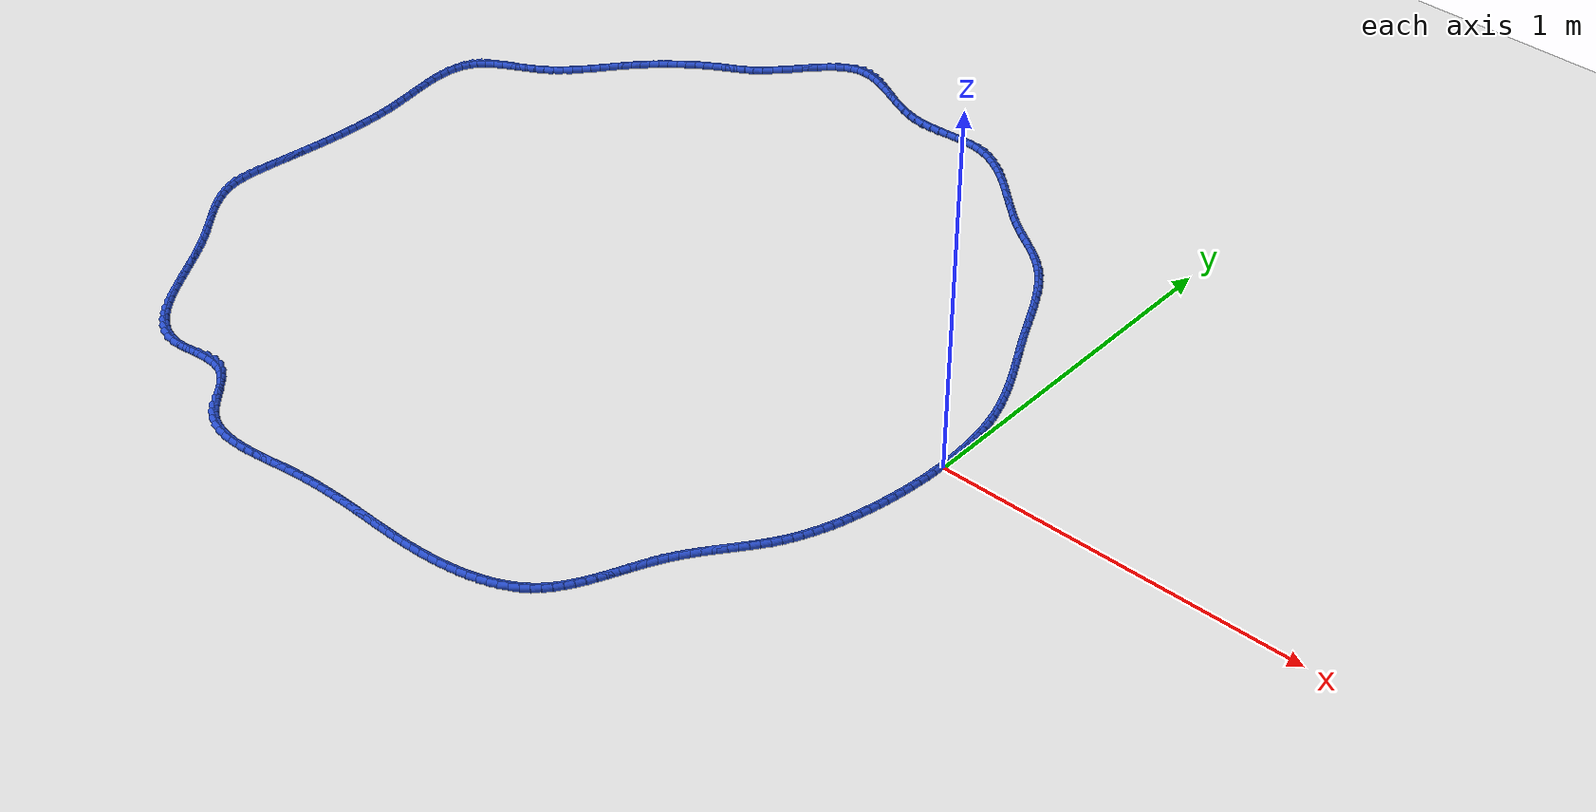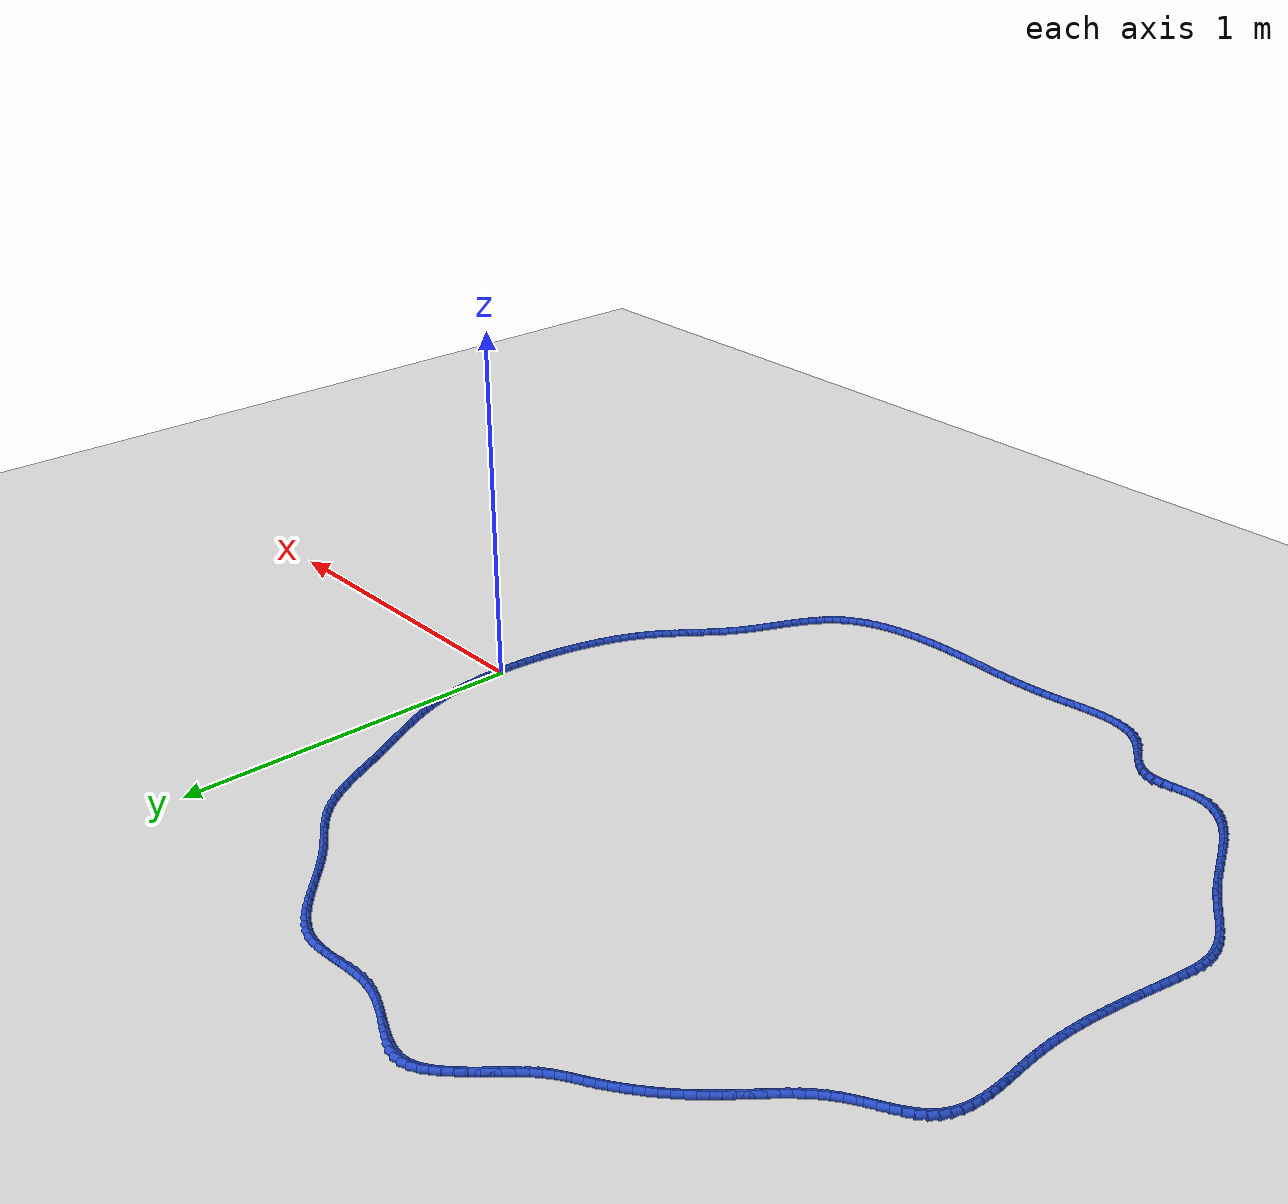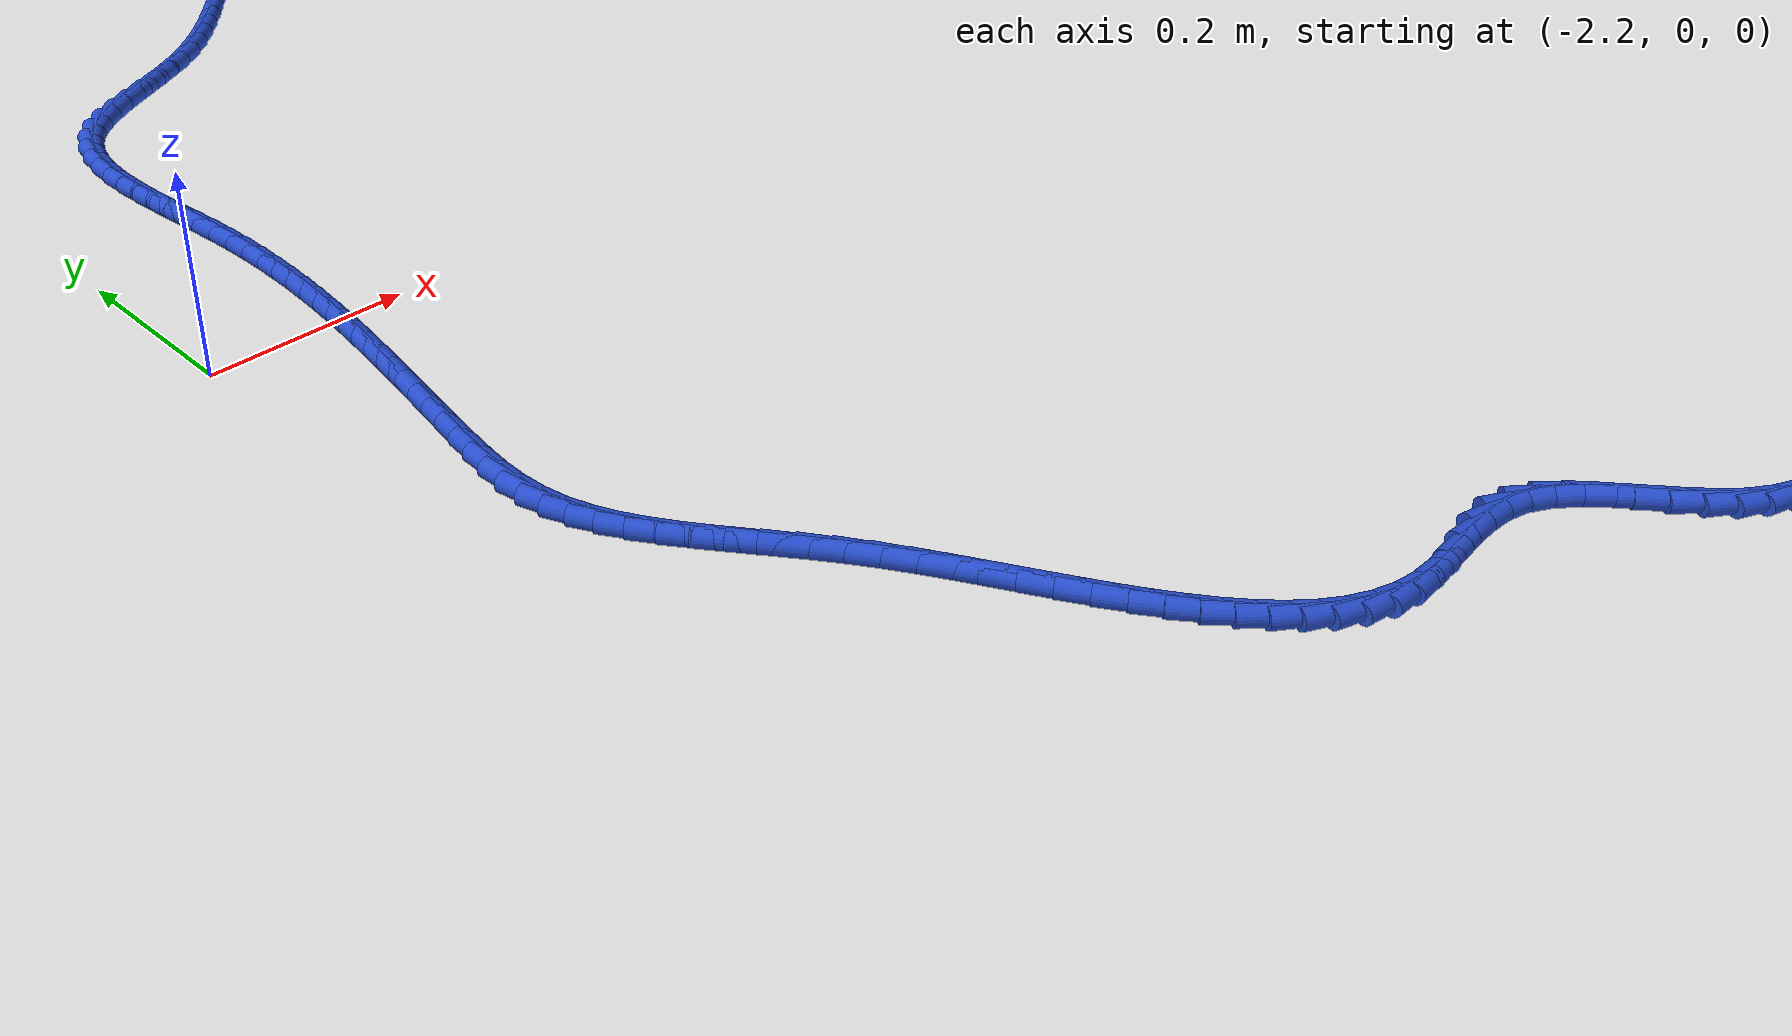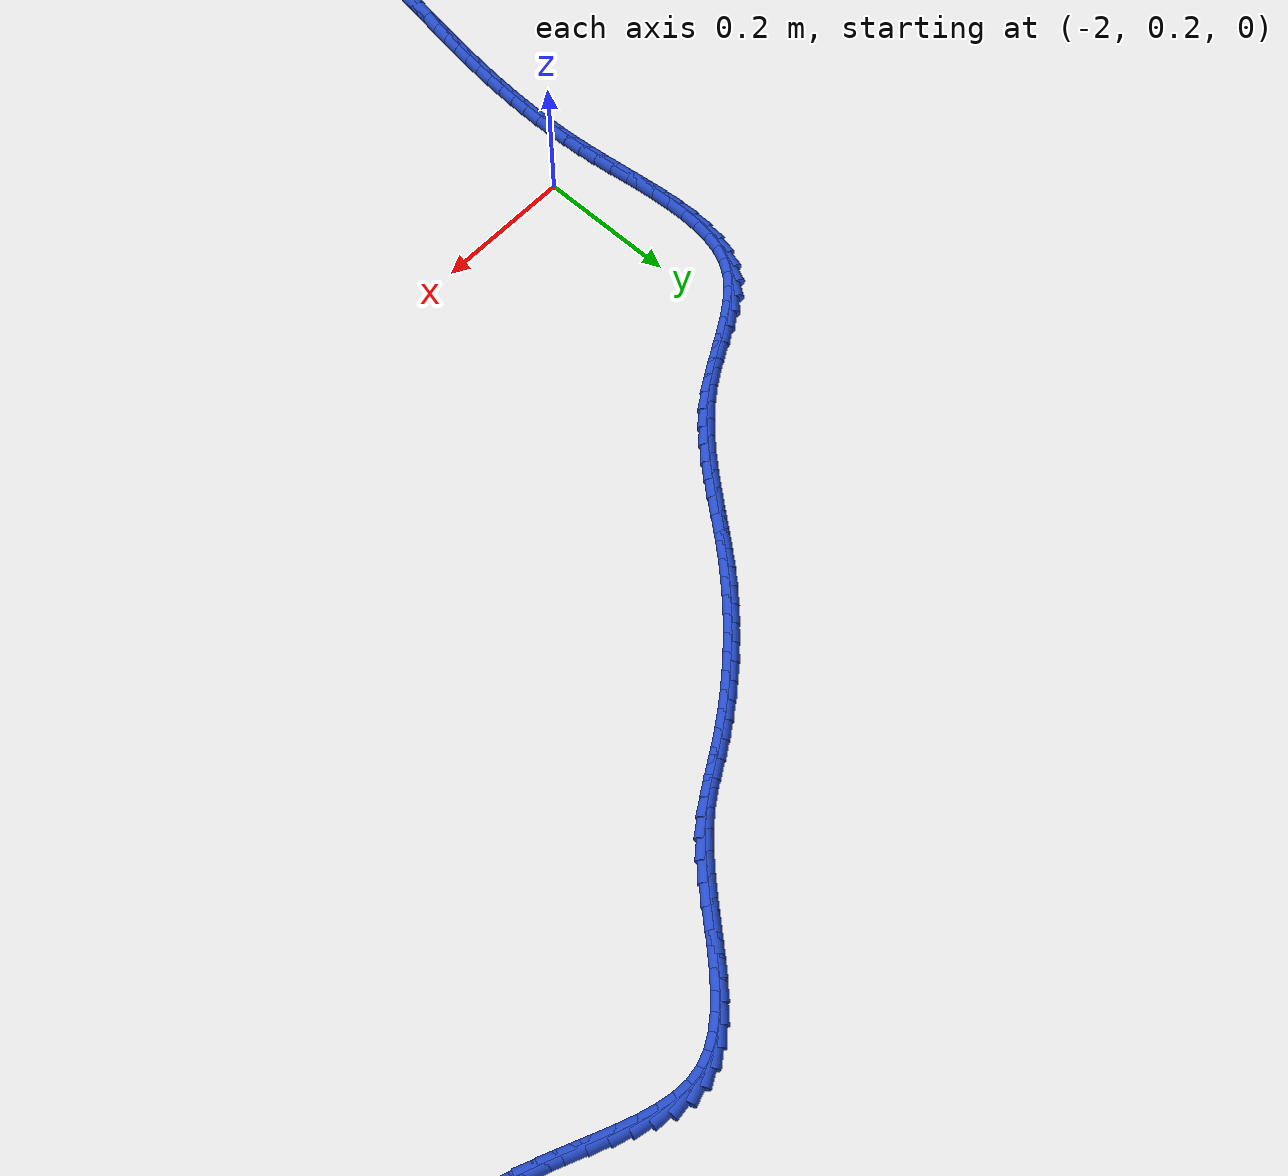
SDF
<sdf version="1.6">
 <world name="default">
  <light name="sun" type="directional">
   <pose>0 0 10 0 -0 0</pose>
   <diffuse>0.8 0.8 0.8 1</diffuse>
   <specular>0.2 0.2 0.2 1</specular>
   <attenuation>
    <range>1000</range>
    <constant>0.9</constant>
    <linear>0.01</linear>
    <quadratic>0.001</quadratic>
   </attenuation>
   <direction>-0.5 0.1 -0.9</direction>
  </light>
  <model name="ground_plane">
   <static>1</static>
   <link name="link">
    <collision name="collision">
     <geometry><plane><normal>0 0 1</normal><size>100 100</size></plane></geometry>
     <surface><friction><ode><mu>100</mu><mu2>50</mu2></ode></friction></surface>
    </collision>
    <visual name="visual">
     <cast_shadows>0</cast_shadows>
     <geometry><plane><normal>0 0 1</normal><size>100 100</size></plane></geometry>
     <material>
      <script><uri>file://media/materials/scripts/gazebo.material</uri><name>Gazebo/WhiteGlow</name></script>
     </material>
    </visual>
   </link>
  </model>
  <gravity>0 0 -9.8</gravity>
  <magnetic_field>6e-06 2.3e-05 -4.2e-05</magnetic_field>
  <atmosphere type="adiabatic"/>
  <physics name="default_physics" default="0" type="ode">
   <max_step_size>0.001</max_step_size>
   <real_time_factor>1</real_time_factor>
   <real_time_update_rate>1000</real_time_update_rate>
  </physics>
  <scene><ambient>0.4 0.4 0.4 1</ambient><background>0.7 0.7 0.7 1</background><shadows>1</shadows></scene>
  <spherical_coordinates>
   <surface_model>EARTH_WGS84</surface_model>
   <latitude_deg>0</latitude_deg>
   <longitude_deg>0</longitude_deg>
   <elevation>0</elevation>
   <heading_deg>0</heading_deg>
  </spherical_coordinates>
  <model name="line">
   <link name="link_0">
    <pose>-4.336808689942018e-18 1.3877787807814457e-17 0.01 0 1.57 1.5680417026096576</pose>
    <collision name="collision">
     <geometry><cylinder><radius>0.01</radius><length>0.08</length></cylinder></geometry>
    </collision>
    <visual name="visual">
     <material>
      <script><name>Gazebo/Blue</name><uri>file://media/materials/scripts/gazebo.material</uri></script>
     </material>
     <geometry><cylinder><radius>0.01</radius><length>0.08</length></cylinder></geometry>
    </visual>
   </link>
   <link name="link_1">
    <pose>7.055029583573843e-05 0.025611521807425305 0.01 0 1.57 -1.5491371057237977</pose>
    <collision name="collision">
     <geometry><cylinder><radius>0.01</radius><length>0.08</length></cylinder></geometry>
    </collision>
    <visual name="visual">
     <material>
      <script><name>Gazebo/Blue</name><uri>file://media/materials/scripts/gazebo.material</uri></script>
     </material>
     <geometry><cylinder><radius>0.01</radius><length>0.08</length></cylinder></geometry>
    </visual>
   </link>
   <link name="link_2">
    <pose>-0.00048506980762607114 0.05126033043305126 0.01 0 1.57 -1.522812633808329</pose>
    <collision name="collision">
     <geometry><cylinder><radius>0.01</radius><length>0.08</length></cylinder></geometry>
    </collision>
    <visual name="visual">
     <material>
      <script><name>Gazebo/Blue</name><uri>file://media/materials/scripts/gazebo.material</uri></script>
     </material>
     <geometry><cylinder><radius>0.01</radius><length>0.08</length></cylinder></geometry>
    </visual>
   </link>
   <link name="link_3">
    <pose>-0.0017159725484607558 0.07689316167516233 0.01 0 1.57 -1.494457365363137</pose>
    <collision name="collision">
     <geometry><cylinder><radius>0.01</radius><length>0.08</length></cylinder></geometry>
    </collision>
    <visual name="visual">
     <material>
      <script><name>Gazebo/Blue</name><uri>file://media/materials/scripts/gazebo.material</uri></script>
     </material>
     <geometry><cylinder><radius>0.01</radius><length>0.08</length></cylinder></geometry>
    </visual>
   </link>
   <link name="link_4">
    <pose>-0.0036712701647436327 0.10245675133204282 0.01 0 1.57 -1.4639450725006127</pose>
    <collision name="collision">
     <geometry><cylinder><radius>0.01</radius><length>0.08</length></cylinder></geometry>
    </collision>
    <visual name="visual">
     <material>
      <script><name>Gazebo/Blue</name><uri>file://media/materials/scripts/gazebo.material</uri></script>
     </material>
     <geometry><cylinder><radius>0.01</radius><length>0.08</length></cylinder></geometry>
    </visual>
   </link>
   <link name="link_5">
    <pose>-0.006400074894550021 0.12789783520197714 0.01 0 1.57 -1.4311460862650385</pose>
    <collision name="collision">
     <geometry><cylinder><radius>0.01</radius><length>0.08</length></cylinder></geometry>
    </collision>
    <visual name="visual">
     <material>
      <script><name>Gazebo/Blue</name><uri>file://media/materials/scripts/gazebo.material</uri></script>
     </material>
     <geometry><cylinder><radius>0.01</radius><length>0.08</length></cylinder></geometry>
    </visual>
   </link>
   <link name="link_6">
    <pose>-0.009951498975955243 0.1531631490832497 0.01 0 1.57 -1.3959308947107396</pose>
    <collision name="collision">
     <geometry><cylinder><radius>0.01</radius><length>0.08</length></cylinder></geometry>
    </collision>
    <visual name="visual">
     <material>
      <script><name>Gazebo/Blue</name><uri>file://media/materials/scripts/gazebo.material</uri></script>
     </material>
     <geometry><cylinder><radius>0.01</radius><length>0.08</length></cylinder></geometry>
    </visual>
   </link>
   <link name="link_7">
    <pose>-0.014374654647034621 0.17819942877414496 0.01 0 1.57 -1.3581749533216638</pose>
    <collision name="collision">
     <geometry><cylinder><radius>0.01</radius><length>0.08</length></cylinder></geometry>
    </collision>
    <visual name="visual">
     <material>
      <script><name>Gazebo/Blue</name><uri>file://media/materials/scripts/gazebo.material</uri></script>
     </material>
     <geometry><cylinder><radius>0.01</radius><length>0.08</length></cylinder></geometry>
    </visual>
   </link>
   <link name="link_8">
    <pose>-0.019718654145863462 0.2029534100729472 0.01 0 1.57 -1.3177649226880668</pose>
    <collision name="collision">
     <geometry><cylinder><radius>0.01</radius><length>0.08</length></cylinder></geometry>
    </collision>
    <visual name="visual">
     <material>
      <script><name>Gazebo/Blue</name><uri>file://media/materials/scripts/gazebo.material</uri></script>
     </material>
     <geometry><cylinder><radius>0.01</radius><length>0.08</length></cylinder></geometry>
    </visual>
   </link>
   <link name="link_9">
    <pose>-0.026032609710517095 0.22737182877794082 0.01 0 1.57 -1.275369090368251</pose>
    <collision name="collision">
     <geometry><cylinder><radius>0.01</radius><length>0.08</length></cylinder></geometry>
    </collision>
    <visual name="visual">
     <material>
      <script><name>Gazebo/Blue</name><uri>file://media/materials/scripts/gazebo.material</uri></script>
     </material>
     <geometry><cylinder><radius>0.01</radius><length>0.08</length></cylinder></geometry>
    </visual>
   </link>
   <link name="link_10">
    <pose>-0.03334909648308402 0.25141288774580556 0.01 0 1.57 -1.235606407601596</pose>
    <collision name="collision">
     <geometry><cylinder><radius>0.01</radius><length>0.08</length></cylinder></geometry>
    </collision>
    <visual name="visual">
     <material>
      <script><name>Gazebo/Blue</name><uri>file://media/materials/scripts/gazebo.material</uri></script>
     </material>
     <geometry><cylinder><radius>0.01</radius><length>0.08</length></cylinder></geometry>
    </visual>
   </link>
   <link name="link_11">
    <pose>-0.041601393582262176 0.2751036431131158 0.01 0 1.57 -1.2003809797950418</pose>
    <collision name="collision">
     <geometry><cylinder><radius>0.01</radius><length>0.08</length></cylinder></geometry>
    </collision>
    <visual name="visual">
     <material>
      <script><name>Gazebo/Blue</name><uri>file://media/materials/scripts/gazebo.material</uri></script>
     </material>
     <geometry><cylinder><radius>0.01</radius><length>0.08</length></cylinder></geometry>
    </visual>
   </link>
   <link name="link_12">
    <pose>-0.050685890326047825 0.2984967309307895 0.01 0 1.57 -1.1698377883868836</pose>
    <collision name="collision">
     <geometry><cylinder><radius>0.01</radius><length>0.08</length></cylinder></geometry>
    </collision>
    <visual name="visual">
     <material>
      <script><name>Gazebo/Blue</name><uri>file://media/materials/scripts/gazebo.material</uri></script>
     </material>
     <geometry><cylinder><radius>0.01</radius><length>0.08</length></cylinder></geometry>
    </visual>
   </link>
   <link name="link_13">
    <pose>-0.06049891474358161 0.32164482974831193 0.01 0 1.57 -1.1440449770562544</pose>
    <collision name="collision">
     <geometry><cylinder><radius>0.01</radius><length>0.08</length></cylinder></geometry>
    </collision>
    <visual name="visual">
     <material>
      <script><name>Gazebo/Blue</name><uri>file://media/materials/scripts/gazebo.material</uri></script>
     </material>
     <geometry><cylinder><radius>0.01</radius><length>0.08</length></cylinder></geometry>
    </visual>
   </link>
   <link name="link_14">
    <pose>-0.07093679486400416 0.3446006181151686 0.01 0 1.57 -1.1230160361813752</pose>
    <collision name="collision">
     <geometry><cylinder><radius>0.01</radius><length>0.08</length></cylinder></geometry>
    </collision>
    <visual name="visual">
     <material>
      <script><name>Gazebo/Blue</name><uri>file://media/materials/scripts/gazebo.material</uri></script>
     </material>
     <geometry><cylinder><radius>0.01</radius><length>0.08</length></cylinder></geometry>
    </visual>
   </link>
   <link name="link_15">
    <pose>-0.08189585871645608 0.3674167745808446 0.01 0 1.57 -1.106727355614148</pose>
    <collision name="collision">
     <geometry><cylinder><radius>0.01</radius><length>0.08</length></cylinder></geometry>
    </collision>
    <visual name="visual">
     <material>
      <script><name>Gazebo/Blue</name><uri>file://media/materials/scripts/gazebo.material</uri></script>
     </material>
     <geometry><cylinder><radius>0.01</radius><length>0.08</length></cylinder></geometry>
    </visual>
   </link>
   <link name="link_16">
    <pose>-0.09327243433007798 0.39014597769482534 0.01 0 1.57 -1.0951328415391106</pose>
    <collision name="collision">
     <geometry><cylinder><radius>0.01</radius><length>0.08</length></cylinder></geometry>
    </collision>
    <visual name="visual">
     <material>
      <script><name>Gazebo/Blue</name><uri>file://media/materials/scripts/gazebo.material</uri></script>
     </material>
     <geometry><cylinder><radius>0.01</radius><length>0.08</length></cylinder></geometry>
    </visual>
   </link>
   <link name="link_17">
    <pose>-0.10496284973401057 0.4128409060065961 0.01 0 1.57 -1.0881751250278064</pose>
    <collision name="collision">
     <geometry><cylinder><radius>0.01</radius><length>0.08</length></cylinder></geometry>
    </collision>
    <visual name="visual">
     <material>
      <script><name>Gazebo/Blue</name><uri>file://media/materials/scripts/gazebo.material</uri></script>
     </material>
     <geometry><cylinder><radius>0.01</radius><length>0.08</length></cylinder></geometry>
    </visual>
   </link>
   <link name="link_18">
    <pose>-0.11686343295739435 0.4355542380656421 0.01 0 1.57 -1.085793312610284</pose>
    <collision name="collision">
     <geometry><cylinder><radius>0.01</radius><length>0.08</length></cylinder></geometry>
    </collision>
    <visual name="visual">
     <material>
      <script><name>Gazebo/Blue</name><uri>file://media/materials/scripts/gazebo.material</uri></script>
     </material>
     <geometry><cylinder><radius>0.01</radius><length>0.08</length></cylinder></geometry>
    </visual>
   </link>
   <link name="link_19">
    <pose>-0.12887051202937005 0.4583386524214487 0.01 0 1.57 -1.087927451853636</pose>
    <collision name="collision">
     <geometry><cylinder><radius>0.01</radius><length>0.08</length></cylinder></geometry>
    </collision>
    <visual name="visual">
     <material>
      <script><name>Gazebo/Blue</name><uri>file://media/materials/scripts/gazebo.material</uri></script>
     </material>
     <geometry><cylinder><radius>0.01</radius><length>0.08</length></cylinder></geometry>
    </visual>
   </link>
   <link name="link_20">
    <pose>-0.14088041497907822 0.48124682762350124 0.01 0 1.57 -1.0945199679432143</pose>
    <collision name="collision">
     <geometry><cylinder><radius>0.01</radius><length>0.08</length></cylinder></geometry>
    </collision>
    <visual name="visual">
     <material>
      <script><name>Gazebo/Blue</name><uri>file://media/materials/scripts/gazebo.material</uri></script>
     </material>
     <geometry><cylinder><radius>0.01</radius><length>0.08</length></cylinder></geometry>
    </visual>
   </link>
   <link name="link_21">
    <pose>-0.15278946983565958 0.5043314422212849 0.01 0 1.57 -1.105394530843542</pose>
    <collision name="collision">
     <geometry><cylinder><radius>0.01</radius><length>0.08</length></cylinder></geometry>
    </collision>
    <visual name="visual">
     <material>
      <script><name>Gazebo/Blue</name><uri>file://media/materials/scripts/gazebo.material</uri></script>
     </material>
     <geometry><cylinder><radius>0.01</radius><length>0.08</length></cylinder></geometry>
    </visual>
   </link>
   <link name="link_22">
    <pose>-0.16449650476497268 0.5276431893219367 0.01 0 1.57 -1.1158279894619605</pose>
    <collision name="collision">
     <geometry><cylinder><radius>0.01</radius><length>0.08</length></cylinder></geometry>
    </collision>
    <visual name="visual">
     <material>
      <script><name>Gazebo/Blue</name><uri>file://media/materials/scripts/gazebo.material</uri></script>
     </material>
     <geometry><cylinder><radius>0.01</radius><length>0.08</length></cylinder></geometry>
    </visual>
   </link>
   <link name="link_23">
    <pose>-0.1759983806410735 0.5511549109738976 0.01 0 1.57 -1.1197820143163177</pose>
    <collision name="collision">
     <geometry><cylinder><radius>0.01</radius><length>0.08</length></cylinder></geometry>
    </collision>
    <visual name="visual">
     <material>
      <script><name>Gazebo/Blue</name><uri>file://media/materials/scripts/gazebo.material</uri></script>
     </material>
     <geometry><cylinder><radius>0.01</radius><length>0.08</length></cylinder></geometry>
    </visual>
   </link>
   <link name="link_24">
    <pose>-0.18741979432647132 0.5747379303833419 0.01 0 1.57 -1.1168957354018232</pose>
    <collision name="collision">
     <geometry><cylinder><radius>0.01</radius><length>0.08</length></cylinder></geometry>
    </collision>
    <visual name="visual">
     <material>
      <script><name>Gazebo/Blue</name><uri>file://media/materials/scripts/gazebo.material</uri></script>
     </material>
     <geometry><cylinder><radius>0.01</radius><length>0.08</length></cylinder></geometry>
    </visual>
   </link>
   <link name="link_25">
    <pose>-0.1988940354471787 0.5982567469549984 0.01 0 1.57 -1.1071212175472944</pose>
    <collision name="collision">
     <geometry><cylinder><radius>0.01</radius><length>0.08</length></cylinder></geometry>
    </collision>
    <visual name="visual">
     <material>
      <script><name>Gazebo/Blue</name><uri>file://media/materials/scripts/gazebo.material</uri></script>
     </material>
     <geometry><cylinder><radius>0.01</radius><length>0.08</length></cylinder></geometry>
    </visual>
   </link>
   <link name="link_26">
    <pose>-0.2105543936292081 0.6215758600935963 0.01 0 1.57 -1.0903140474061312</pose>
    <collision name="collision">
     <geometry><cylinder><radius>0.01</radius><length>0.08</length></cylinder></geometry>
    </collision>
    <visual name="visual">
     <material>
      <script><name>Gazebo/Blue</name><uri>file://media/materials/scripts/gazebo.material</uri></script>
     </material>
     <geometry><cylinder><radius>0.01</radius><length>0.08</length></cylinder></geometry>
    </visual>
   </link>
   <link name="link_27">
    <pose>-0.22253415849857214 0.6445597692038644 0.01 0 1.57 -1.0662428311521037</pose>
    <collision name="collision">
     <geometry><cylinder><radius>0.01</radius><length>0.08</length></cylinder></geometry>
    </collision>
    <visual name="visual">
     <material>
      <script><name>Gazebo/Blue</name><uri>file://media/materials/scripts/gazebo.material</uri></script>
     </material>
     <geometry><cylinder><radius>0.01</radius><length>0.08</length></cylinder></geometry>
    </visual>
   </link>
   <link name="link_28">
    <pose>-0.23496661968128338 0.667072973690532 0.01 0 1.57 -1.0346083159331834</pose>
    <collision name="collision">
     <geometry><cylinder><radius>0.01</radius><length>0.08</length></cylinder></geometry>
    </collision>
    <visual name="visual">
     <material>
      <script><name>Gazebo/Blue</name><uri>file://media/materials/scripts/gazebo.material</uri></script>
     </material>
     <geometry><cylinder><radius>0.01</radius><length>0.08</length></cylinder></geometry>
    </visual>
   </link>
   <link name="link_29">
    <pose>-0.24798506680335436 0.6889799729583277 0.01 0 1.57 -0.9950763039774384</pose>
    <collision name="collision">
     <geometry><cylinder><radius>0.01</radius><length>0.08</length></cylinder></geometry>
    </collision>
    <visual name="visual">
     <material>
      <script><name>Gazebo/Blue</name><uri>file://media/materials/scripts/gazebo.material</uri></script>
     </material>
     <geometry><cylinder><radius>0.01</radius><length>0.08</length></cylinder></geometry>
    </visual>
   </link>
   <link name="link_30">
    <pose>-0.26172278949079764 0.7101452664119807 0.01 0 1.57 -0.9473297229712957</pose>
    <collision name="collision">
     <geometry><cylinder><radius>0.01</radius><length>0.08</length></cylinder></geometry>
    </collision>
    <visual name="visual">
     <material>
      <script><name>Gazebo/Blue</name><uri>file://media/materials/scripts/gazebo.material</uri></script>
     </material>
     <geometry><cylinder><radius>0.01</radius><length>0.08</length></cylinder></geometry>
    </visual>
   </link>
   <link name="link_31">
    <pose>-0.2763130773696256 0.73043335345622 0.01 0 1.57 -0.8911449999154133</pose>
    <collision name="collision">
     <geometry><cylinder><radius>0.01</radius><length>0.08</length></cylinder></geometry>
    </collision>
    <visual name="visual">
     <material>
      <script><name>Gazebo/Blue</name><uri>file://media/materials/scripts/gazebo.material</uri></script>
     </material>
     <geometry><cylinder><radius>0.01</radius><length>0.08</length></cylinder></geometry>
    </visual>
   </link>
   <link name="link_32">
    <pose>-0.29188922006585105 0.7497087334957746 0.01 0 1.57 -0.8264946027217694</pose>
    <collision name="collision">
     <geometry><cylinder><radius>0.01</radius><length>0.08</length></cylinder></geometry>
    </collision>
    <visual name="visual">
     <material>
      <script><name>Gazebo/Blue</name><uri>file://media/materials/scripts/gazebo.material</uri></script>
     </material>
     <geometry><cylinder><radius>0.01</radius><length>0.08</length></cylinder></geometry>
    </visual>
   </link>
   <link name="link_33">
    <pose>-0.3085845072054865 0.7678359059353737 0.01 0 1.57 -0.7543454025134546</pose>
    <collision name="collision">
     <geometry><cylinder><radius>0.01</radius><length>0.08</length></cylinder></geometry>
    </collision>
    <visual name="visual">
     <material>
      <script><name>Gazebo/Blue</name><uri>file://media/materials/scripts/gazebo.material</uri></script>
     </material>
     <geometry><cylinder><radius>0.01</radius><length>0.08</length></cylinder></geometry>
    </visual>
   </link>
   <link name="link_34">
    <pose>-0.3265219029304062 0.7846925046535169 0.01 0 1.57 -0.6880054036686947</pose>
    <collision name="collision">
     <geometry><cylinder><radius>0.01</radius><length>0.08</length></cylinder></geometry>
    </collision>
    <visual name="visual">
     <material>
      <script><name>Gazebo/Blue</name><uri>file://media/materials/scripts/gazebo.material</uri></script>
     </material>
     <geometry><cylinder><radius>0.01</radius><length>0.08</length></cylinder></geometry>
    </visual>
   </link>
   <link name="link_35">
    <pose>-0.3456320414955044 0.8004008156749937 0.01 0 1.57 -0.6392162142944259</pose>
    <collision name="collision">
     <geometry><cylinder><radius>0.01</radius><length>0.08</length></cylinder></geometry>
    </collision>
    <visual name="visual">
     <material>
      <script><name>Gazebo/Blue</name><uri>file://media/materials/scripts/gazebo.material</uri></script>
     </material>
     <geometry><cylinder><radius>0.01</radius><length>0.08</length></cylinder></geometry>
    </visual>
   </link>
   <link name="link_36">
    <pose>-0.3656754010465393 0.8152995711420333 0.01 0 1.57 -0.6082472600852731</pose>
    <collision name="collision">
     <geometry><cylinder><radius>0.01</radius><length>0.08</length></cylinder></geometry>
    </collision>
    <visual name="visual">
     <material>
      <script><name>Gazebo/Blue</name><uri>file://media/materials/scripts/gazebo.material</uri></script>
     </material>
     <geometry><cylinder><radius>0.01</radius><length>0.08</length></cylinder></geometry>
    </visual>
   </link>
   <link name="link_37">
    <pose>-0.38640658987141224 0.8297349699163937 0.01 0 1.57 -0.5945941688032522</pose>
    <collision name="collision">
     <geometry><cylinder><radius>0.01</radius><length>0.08</length></cylinder></geometry>
    </collision>
    <visual name="visual">
     <material>
      <script><name>Gazebo/Blue</name><uri>file://media/materials/scripts/gazebo.material</uri></script>
     </material>
     <geometry><cylinder><radius>0.01</radius><length>0.08</length></cylinder></geometry>
    </visual>
   </link>
   <link name="link_38">
    <pose>-0.40758021625802465 0.8440532108598324 0.01 0 1.57 -0.5976636535230972</pose>
    <collision name="collision">
     <geometry><cylinder><radius>0.01</radius><length>0.08</length></cylinder></geometry>
    </collision>
    <visual name="visual">
     <material>
      <script><name>Gazebo/Blue</name><uri>file://media/materials/scripts/gazebo.material</uri></script>
     </material>
     <geometry><cylinder><radius>0.01</radius><length>0.08</length></cylinder></geometry>
    </visual>
   </link>
   <link name="link_39">
    <pose>-0.42895088849427787 0.8586004928341079 0.01 0 1.57 -0.6168965279006676</pose>
    <collision name="collision">
     <geometry><cylinder><radius>0.01</radius><length>0.08</length></cylinder></geometry>
    </collision>
    <visual name="visual">
     <material>
      <script><name>Gazebo/Blue</name><uri>file://media/materials/scripts/gazebo.material</uri></script>
     </material>
     <geometry><cylinder><radius>0.01</radius><length>0.08</length></cylinder></geometry>
    </visual>
   </link>
   <link name="link_40">
    <pose>-0.4502732148680729 0.8737230147009769 0.01 0 1.57 -0.6514691453298563</pose>
    <collision name="collision">
     <geometry><cylinder><radius>0.01</radius><length>0.08</length></cylinder></geometry>
    </collision>
    <visual name="visual">
     <material>
      <script><name>Gazebo/Blue</name><uri>file://media/materials/scripts/gazebo.material</uri></script>
     </material>
     <geometry><cylinder><radius>0.01</radius><length>0.08</length></cylinder></geometry>
    </visual>
   </link>
   <link name="link_41">
    <pose>-0.4713052228606581 0.8897604502327771 0.01 0 1.57 -0.6899381625758085</pose>
    <collision name="collision">
     <geometry><cylinder><radius>0.01</radius><length>0.08</length></cylinder></geometry>
    </collision>
    <visual name="visual">
     <material>
      <script><name>Gazebo/Blue</name><uri>file://media/materials/scripts/gazebo.material</uri></script>
     </material>
     <geometry><cylinder><radius>0.01</radius><length>0.08</length></cylinder></geometry>
    </visual>
   </link>
   <link name="link_42">
    <pose>-0.49194212056158304 0.9067906817073801 0.01 0 1.57 -0.7182182246020294</pose>
    <collision name="collision">
     <geometry><cylinder><radius>0.01</radius><length>0.08</length></cylinder></geometry>
    </collision>
    <visual name="visual">
     <material>
      <script><name>Gazebo/Blue</name><uri>file://media/materials/scripts/gazebo.material</uri></script>
     </material>
     <geometry><cylinder><radius>0.01</radius><length>0.08</length></cylinder></geometry>
    </visual>
   </link>
   <link name="link_43">
    <pose>-0.5122598226105306 0.9245467362631078 0.01 0 1.57 -0.7359224903440341</pose>
    <collision name="collision">
     <geometry><cylinder><radius>0.01</radius><length>0.08</length></cylinder></geometry>
    </collision>
    <visual name="visual">
     <material>
      <script><name>Gazebo/Blue</name><uri>file://media/materials/scripts/gazebo.material</uri></script>
     </material>
     <geometry><cylinder><radius>0.01</radius><length>0.08</length></cylinder></geometry>
    </visual>
   </link>
   <link name="link_44">
    <pose>-0.5323465757926781 0.9427381067294724 0.01 0 1.57 -0.7434201676575527</pose>
    <collision name="collision">
     <geometry><cylinder><radius>0.01</radius><length>0.08</length></cylinder></geometry>
    </collision>
    <visual name="visual">
     <material>
      <script><name>Gazebo/Blue</name><uri>file://media/materials/scripts/gazebo.material</uri></script>
     </material>
     <geometry><cylinder><radius>0.01</radius><length>0.08</length></cylinder></geometry>
    </visual>
   </link>
   <link name="link_45">
    <pose>-0.5522906268932026 0.9610742859359854 0.01 0 1.57 -0.7408082115172868</pose>
    <collision name="collision">
     <geometry><cylinder><radius>0.01</radius><length>0.08</length></cylinder></geometry>
    </collision>
    <visual name="visual">
     <material>
      <script><name>Gazebo/Blue</name><uri>file://media/materials/scripts/gazebo.material</uri></script>
     </material>
     <geometry><cylinder><radius>0.01</radius><length>0.08</length></cylinder></geometry>
    </visual>
   </link>
   <link name="link_46">
    <pose>-0.5721802226972806 0.9792647667121582 0.01 0 1.57 -0.7278913982920897</pose>
    <collision name="collision">
     <geometry><cylinder><radius>0.01</radius><length>0.08</length></cylinder></geometry>
    </collision>
    <visual name="visual">
     <material>
      <script><name>Gazebo/Blue</name><uri>file://media/materials/scripts/gazebo.material</uri></script>
     </material>
     <geometry><cylinder><radius>0.01</radius><length>0.08</length></cylinder></geometry>
    </visual>
   </link>
   <link name="link_47">
    <pose>-0.5921036099900893 0.9970190418875027 0.01 0 1.57 -0.704173968811788</pose>
    <collision name="collision">
     <geometry><cylinder><radius>0.01</radius><length>0.08</length></cylinder></geometry>
    </collision>
    <visual name="visual">
     <material>
      <script><name>Gazebo/Blue</name><uri>file://media/materials/scripts/gazebo.material</uri></script>
     </material>
     <geometry><cylinder><radius>0.01</radius><length>0.08</length></cylinder></geometry>
    </visual>
   </link>
   <link name="link_48">
    <pose>-0.6121490355568059 1.0140466042915302 0.01 0 1.57 -0.6688667619999197</pose>
    <collision name="collision">
     <geometry><cylinder><radius>0.01</radius><length>0.08</length></cylinder></geometry>
    </collision>
    <visual name="visual">
     <material>
      <script><name>Gazebo/Blue</name><uri>file://media/materials/scripts/gazebo.material</uri></script>
     </material>
     <geometry><cylinder><radius>0.01</radius><length>0.08</length></cylinder></geometry>
    </visual>
   </link>
   <link name="link_49">
    <pose>-0.632404746182607 1.0300569467537526 0.01 0 1.57 -0.6209261187613998</pose>
    <collision name="collision">
     <geometry><cylinder><radius>0.01</radius><length>0.08</length></cylinder></geometry>
    </collision>
    <visual name="visual">
     <material>
      <script><name>Gazebo/Blue</name><uri>file://media/materials/scripts/gazebo.material</uri></script>
     </material>
     <geometry><cylinder><radius>0.01</radius><length>0.08</length></cylinder></geometry>
    </visual>
   </link>
   <link name="link_50">
    <pose>-0.6529589886526693 1.0447595621036814 0.01 0 1.57 -0.5591568909061799</pose>
    <collision name="collision">
     <geometry><cylinder><radius>0.01</radius><length>0.08</length></cylinder></geometry>
    </collision>
    <visual name="visual">
     <material>
      <script><name>Gazebo/Blue</name><uri>file://media/materials/scripts/gazebo.material</uri></script>
     </material>
     <geometry><cylinder><radius>0.01</radius><length>0.08</length></cylinder></geometry>
    </visual>
   </link>
   <link name="link_51">
    <pose>-0.6739000097521701 1.0578639431708279 0.01 0 1.57 -0.482429402145706</pose>
    <collision name="collision">
     <geometry><cylinder><radius>0.01</radius><length>0.08</length></cylinder></geometry>
    </collision>
    <visual name="visual">
     <material>
      <script><name>Gazebo/Blue</name><uri>file://media/materials/scripts/gazebo.material</uri></script>
     </material>
     <geometry><cylinder><radius>0.01</radius><length>0.08</length></cylinder></geometry>
    </visual>
   </link>
   <link name="link_52">
    <pose>-0.6953160562662866 1.0690795827847042 0.01 0 1.57 -0.39006554121711307</pose>
    <collision name="collision">
     <geometry><cylinder><radius>0.01</radius><length>0.08</length></cylinder></geometry>
    </collision>
    <visual name="visual">
     <material>
      <script><name>Gazebo/Blue</name><uri>file://media/materials/scripts/gazebo.material</uri></script>
     </material>
     <geometry><cylinder><radius>0.01</radius><length>0.08</length></cylinder></geometry>
    </visual>
   </link>
   <link name="link_53">
    <pose>-0.7172953749801951 1.0781159737748216 0.01 0 1.57 -0.28240791062232945</pose>
    <collision name="collision">
     <geometry><cylinder><radius>0.01</radius><length>0.08</length></cylinder></geometry>
    </collision>
    <visual name="visual">
     <material>
      <script><name>Gazebo/Blue</name><uri>file://media/materials/scripts/gazebo.material</uri></script>
     </material>
     <geometry><cylinder><radius>0.01</radius><length>0.08</length></cylinder></geometry>
    </visual>
   </link>
   <link name="link_54">
    <pose>-0.7399262126790731 1.084682608970692 0.01 0 1.57 -0.1624743468708019</pose>
    <collision name="collision">
     <geometry><cylinder><radius>0.01</radius><length>0.08</length></cylinder></geometry>
    </collision>
    <visual name="visual">
     <material>
      <script><name>Gazebo/Blue</name><uri>file://media/materials/scripts/gazebo.material</uri></script>
     </material>
     <geometry><cylinder><radius>0.01</radius><length>0.08</length></cylinder></geometry>
    </visual>
   </link>
   <link name="link_55">
    <pose>-0.7632921904338535 1.088512742921414 0.01 0 1.57 -0.05458860557553595</pose>
    <collision name="collision">
     <geometry><cylinder><radius>0.01</radius><length>0.08</length></cylinder></geometry>
    </collision>
    <visual name="visual">
     <material>
      <script><name>Gazebo/Blue</name><uri>file://media/materials/scripts/gazebo.material</uri></script>
     </material>
     <geometry><cylinder><radius>0.01</radius><length>0.08</length></cylinder></geometry>
    </visual>
   </link>
   <link name="link_56">
    <pose>-0.7873816514433528 1.0898290607722927 0.01 0 1.57 0.02084299876790048</pose>
    <collision name="collision">
     <geometry><cylinder><radius>0.01</radius><length>0.08</length></cylinder></geometry>
    </collision>
    <visual name="visual">
     <material>
      <script><name>Gazebo/Blue</name><uri>file://media/materials/scripts/gazebo.material</uri></script>
     </material>
     <geometry><cylinder><radius>0.01</radius><length>0.08</length></cylinder></geometry>
    </visual>
   </link>
   <link name="link_57">
    <pose>-0.8120934544725048 1.0893139180921287 0.01 0 1.57 0.06516623522086187</pose>
    <collision name="collision">
     <geometry><cylinder><radius>0.01</radius><length>0.08</length></cylinder></geometry>
    </collision>
    <visual name="visual">
     <material>
      <script><name>Gazebo/Blue</name><uri>file://media/materials/scripts/gazebo.material</uri></script>
     </material>
     <geometry><cylinder><radius>0.01</radius><length>0.08</length></cylinder></geometry>
    </visual>
   </link>
   <link name="link_58">
    <pose>-0.8373229926892825 1.0876674727909166 0.01 0 1.57 0.08084423676909384</pose>
    <collision name="collision">
     <geometry><cylinder><radius>0.01</radius><length>0.08</length></cylinder></geometry>
    </collision>
    <visual name="visual">
     <material>
      <script><name>Gazebo/Blue</name><uri>file://media/materials/scripts/gazebo.material</uri></script>
     </material>
     <geometry><cylinder><radius>0.01</radius><length>0.08</length></cylinder></geometry>
    </visual>
   </link>
   <link name="link_59">
    <pose>-0.8629656592616574 1.0855898827786497 0.01 0 1.57 0.06957898353205035</pose>
    <collision name="collision">
     <geometry><cylinder><radius>0.01</radius><length>0.08</length></cylinder></geometry>
    </collision>
    <visual name="visual">
     <material>
      <script><name>Gazebo/Blue</name><uri>file://media/materials/scripts/gazebo.material</uri></script>
     </material>
     <geometry><cylinder><radius>0.01</radius><length>0.08</length></cylinder></geometry>
    </visual>
   </link>
   <link name="link_60">
    <pose>-0.8889168473576017 1.0837813059653219 0.01 0 1.57 0.03208237021182199</pose>
    <collision name="collision">
     <geometry><cylinder><radius>0.01</radius><length>0.08</length></cylinder></geometry>
    </collision>
    <visual name="visual">
     <material>
      <script><name>Gazebo/Blue</name><uri>file://media/materials/scripts/gazebo.material</uri></script>
     </material>
     <geometry><cylinder><radius>0.01</radius><length>0.08</length></cylinder></geometry>
    </visual>
   </link>
   <link name="link_61">
    <pose>-0.9150719501450874 1.0829419002609264 0.01 0 1.57 -0.03160029221157571</pose>
    <collision name="collision">
     <geometry><cylinder><radius>0.01</radius><length>0.08</length></cylinder></geometry>
    </collision>
    <visual name="visual">
     <material>
      <script><name>Gazebo/Blue</name><uri>file://media/materials/scripts/gazebo.material</uri></script>
     </material>
     <geometry><cylinder><radius>0.01</radius><length>0.08</length></cylinder></geometry>
    </visual>
   </link>
   <link name="link_62">
    <pose>-0.9413263607920861 1.083771823575457 0.01 0 1.57 -0.12128814989130518</pose>
    <collision name="collision">
     <geometry><cylinder><radius>0.01</radius><length>0.08</length></cylinder></geometry>
    </collision>
    <visual name="visual">
     <material>
      <script><name>Gazebo/Blue</name><uri>file://media/materials/scripts/gazebo.material</uri></script>
     </material>
     <geometry><cylinder><radius>0.01</radius><length>0.08</length></cylinder></geometry>
    </visual>
   </link>
   <link name="link_63">
    <pose>-0.9675754724665704 1.0869712338189081 0.01 0 1.57 -0.2284625076575297</pose>
    <collision name="collision">
     <geometry><cylinder><radius>0.01</radius><length>0.08</length></cylinder></geometry>
    </collision>
    <visual name="visual">
     <material>
      <script><name>Gazebo/Blue</name><uri>file://media/materials/scripts/gazebo.material</uri></script>
     </material>
     <geometry><cylinder><radius>0.01</radius><length>0.08</length></cylinder></geometry>
    </visual>
   </link>
   <link name="link_64">
    <pose>-0.9937192814764787 1.0930502488189533 0.01 0 1.57 -0.31730649189543103</pose>
    <collision name="collision">
     <geometry><cylinder><radius>0.01</radius><length>0.08</length></cylinder></geometry>
    </collision>
    <visual name="visual">
     <material>
      <script><name>Gazebo/Blue</name><uri>file://media/materials/scripts/gazebo.material</uri></script>
     </material>
     <geometry><cylinder><radius>0.01</radius><length>0.08</length></cylinder></geometry>
    </visual>
   </link>
   <link name="link_65">
    <pose>-1.019680624475829 1.1015760254504083 0.01 0 1.57 -0.37930725209647875</pose>
    <collision name="collision">
     <geometry><cylinder><radius>0.01</radius><length>0.08</length></cylinder></geometry>
    </collision>
    <visual name="visual">
     <material>
      <script><name>Gazebo/Blue</name><uri>file://media/materials/scripts/gazebo.material</uri></script>
     </material>
     <geometry><cylinder><radius>0.01</radius><length>0.08</length></cylinder></geometry>
    </visual>
   </link>
   <link name="link_66">
    <pose>-1.0453894091018305 1.1118237958937458 0.01 0 1.57 -0.4169796591906771</pose>
    <collision name="collision">
     <geometry><cylinder><radius>0.01</radius><length>0.08</length></cylinder></geometry>
    </collision>
    <visual name="visual">
     <material>
      <script><name>Gazebo/Blue</name><uri>file://media/materials/scripts/gazebo.material</uri></script>
     </material>
     <geometry><cylinder><radius>0.01</radius><length>0.08</length></cylinder></geometry>
    </visual>
   </link>
   <link name="link_67">
    <pose>-1.0707755451050622 1.1230687050792298 0.01 0 1.57 -0.4318065948784096</pose>
    <collision name="collision">
     <geometry><cylinder><radius>0.01</radius><length>0.08</length></cylinder></geometry>
    </collision>
    <visual name="visual">
     <material>
      <script><name>Gazebo/Blue</name><uri>file://media/materials/scripts/gazebo.material</uri></script>
     </material>
     <geometry><cylinder><radius>0.01</radius><length>0.08</length></cylinder></geometry>
    </visual>
   </link>
   <link name="link_68">
    <pose>-1.0957689422361025 1.1345858979371257 0.01 0 1.57 -0.4237304479402189</pose>
    <collision name="collision">
     <geometry><cylinder><radius>0.01</radius><length>0.08</length></cylinder></geometry>
    </collision>
    <visual name="visual">
     <material>
      <script><name>Gazebo/Blue</name><uri>file://media/materials/scripts/gazebo.material</uri></script>
     </material>
     <geometry><cylinder><radius>0.01</radius><length>0.08</length></cylinder></geometry>
    </visual>
   </link>
   <link name="link_69">
    <pose>-1.1202995102455309 1.1456505193976976 0.01 0 1.57 -0.39081404400879194</pose>
    <collision name="collision">
     <geometry><cylinder><radius>0.01</radius><length>0.08</length></cylinder></geometry>
    </collision>
    <visual name="visual">
     <material>
      <script><name>Gazebo/Blue</name><uri>file://media/materials/scripts/gazebo.material</uri></script>
     </material>
     <geometry><cylinder><radius>0.01</radius><length>0.08</length></cylinder></geometry>
    </visual>
   </link>
   <link name="link_70">
    <pose>-1.1442971588839248 1.1555377143912107 0.01 0 1.57 -0.32891570914471635</pose>
    <collision name="collision">
     <geometry><cylinder><radius>0.01</radius><length>0.08</length></cylinder></geometry>
    </collision>
    <visual name="visual">
     <material>
      <script><name>Gazebo/Blue</name><uri>file://media/materials/scripts/gazebo.material</uri></script>
     </material>
     <geometry><cylinder><radius>0.01</radius><length>0.08</length></cylinder></geometry>
    </visual>
   </link>
   <link name="link_71">
    <pose>-1.1676917979018644 1.1635226278479285 0.01 0 1.57 -0.23157153831979121</pose>
    <collision name="collision">
     <geometry><cylinder><radius>0.01</radius><length>0.08</length></cylinder></geometry>
    </collision>
    <visual name="visual">
     <material>
      <script><name>Gazebo/Blue</name><uri>file://media/materials/scripts/gazebo.material</uri></script>
     </material>
     <geometry><cylinder><radius>0.01</radius><length>0.08</length></cylinder></geometry>
    </visual>
   </link>
   <link name="link_72">
    <pose>-1.1904133370499284 1.168880404698117 0.01 0 1.57 -0.09100976090152608</pose>
    <collision name="collision">
     <geometry><cylinder><radius>0.01</radius><length>0.08</length></cylinder></geometry>
    </collision>
    <visual name="visual">
     <material>
      <script><name>Gazebo/Blue</name><uri>file://media/materials/scripts/gazebo.material</uri></script>
     </material>
     <geometry><cylinder><radius>0.01</radius><length>0.08</length></cylinder></geometry>
    </visual>
   </link>
   <link name="link_73">
    <pose>-1.2123916860786954 1.1708861898720404 0.01 0 1.57 0.09744494103459894</pose>
    <collision name="collision">
     <geometry><cylinder><radius>0.01</radius><length>0.08</length></cylinder></geometry>
    </collision>
    <visual name="visual">
     <material>
      <script><name>Gazebo/Blue</name><uri>file://media/materials/scripts/gazebo.material</uri></script>
     </material>
     <geometry><cylinder><radius>0.01</radius><length>0.08</length></cylinder></geometry>
    </visual>
   </link>
   <link name="link_74">
    <pose>-1.2335570856744762 1.1688171758213879 0.01 0 1.57 0.3084296139586318</pose>
    <collision name="collision">
     <geometry><cylinder><radius>0.01</radius><length>0.08</length></cylinder></geometry>
    </collision>
    <visual name="visual">
     <material>
      <script><name>Gazebo/Blue</name><uri>file://media/materials/scripts/gazebo.material</uri></script>
     </material>
     <geometry><cylinder><radius>0.01</radius><length>0.08</length></cylinder></geometry>
    </visual>
   </link>
   <link name="link_75">
    <pose>-1.2539019714685462 1.1623353592665024 0.01 0 1.57 0.48662779591839656</pose>
    <collision name="collision">
     <geometry><cylinder><radius>0.01</radius><length>0.08</length></cylinder></geometry>
    </collision>
    <visual name="visual">
     <material>
      <script><name>Gazebo/Blue</name><uri>file://media/materials/scripts/gazebo.material</uri></script>
     </material>
     <geometry><cylinder><radius>0.01</radius><length>0.08</length></cylinder></geometry>
    </visual>
   </link>
   <link name="link_76">
    <pose>-1.273553823532791 1.1519382658800192 0.01 0 1.57 0.62231070719771</pose>
    <collision name="collision">
     <geometry><cylinder><radius>0.01</radius><length>0.08</length></cylinder></geometry>
    </collision>
    <visual name="visual">
     <material>
      <script><name>Gazebo/Blue</name><uri>file://media/materials/scripts/gazebo.material</uri></script>
     </material>
     <geometry><cylinder><radius>0.01</radius><length>0.08</length></cylinder></geometry>
    </visual>
   </link>
   <link name="link_77">
    <pose>-1.2926578312646495 1.138232990111772 0.01 0 1.57 0.7201211053214716</pose>
    <collision name="collision">
     <geometry><cylinder><radius>0.01</radius><length>0.08</length></cylinder></geometry>
    </collision>
    <visual name="visual">
     <material>
      <script><name>Gazebo/Blue</name><uri>file://media/materials/scripts/gazebo.material</uri></script>
     </material>
     <geometry><cylinder><radius>0.01</radius><length>0.08</length></cylinder></geometry>
    </visual>
   </link>
   <link name="link_78">
    <pose>-1.3113591840615595 1.1218266264115935 0.01 0 1.57 0.7869266796724762</pose>
    <collision name="collision">
     <geometry><cylinder><radius>0.01</radius><length>0.08</length></cylinder></geometry>
    </collision>
    <visual name="visual">
     <material>
      <script><name>Gazebo/Blue</name><uri>file://media/materials/scripts/gazebo.material</uri></script>
     </material>
     <geometry><cylinder><radius>0.01</radius><length>0.08</length></cylinder></geometry>
    </visual>
   </link>
   <link name="link_79">
    <pose>-1.3298030713209599 1.1033262692293173 0.01 0 1.57 0.8285783532904871</pose>
    <collision name="collision">
     <geometry><cylinder><radius>0.01</radius><length>0.08</length></cylinder></geometry>
    </collision>
    <visual name="visual">
     <material>
      <script><name>Gazebo/Blue</name><uri>file://media/materials/scripts/gazebo.material</uri></script>
     </material>
     <geometry><cylinder><radius>0.01</radius><length>0.08</length></cylinder></geometry>
    </visual>
   </link>
   <link name="link_80">
    <pose>-1.3481346824402878 1.083339013014777 0.01 0 1.57 0.8491006721655542</pose>
    <collision name="collision">
     <geometry><cylinder><radius>0.01</radius><length>0.08</length></cylinder></geometry>
    </collision>
    <visual name="visual">
     <material>
      <script><name>Gazebo/Blue</name><uri>file://media/materials/scripts/gazebo.material</uri></script>
     </material>
     <geometry><cylinder><radius>0.01</radius><length>0.08</length></cylinder></geometry>
    </visual>
   </link>
   <link name="link_81">
    <pose>-1.3664992068169821 1.062471952217805 0.01 0 1.57 0.8507532141520987</pose>
    <collision name="collision">
     <geometry><cylinder><radius>0.01</radius><length>0.08</length></cylinder></geometry>
    </collision>
    <visual name="visual">
     <material>
      <script><name>Gazebo/Blue</name><uri>file://media/materials/scripts/gazebo.material</uri></script>
     </material>
     <geometry><cylinder><radius>0.01</radius><length>0.08</length></cylinder></geometry>
    </visual>
   </link>
   <link name="link_82">
    <pose>-1.3850418338484816 1.0413321812882352 0.01 0 1.57 0.8342476919728754</pose>
    <collision name="collision">
     <geometry><cylinder><radius>0.01</radius><length>0.08</length></cylinder></geometry>
    </collision>
    <visual name="visual">
     <material>
      <script><name>Gazebo/Blue</name><uri>file://media/materials/scripts/gazebo.material</uri></script>
     </material>
     <geometry><cylinder><radius>0.01</radius><length>0.08</length></cylinder></geometry>
    </visual>
   </link>
   <link name="link_83">
    <pose>-1.4039077529322235 1.0205267946759005 0.01 0 1.57 0.7989057643513876</pose>
    <collision name="collision">
     <geometry><cylinder><radius>0.01</radius><length>0.08</length></cylinder></geometry>
    </collision>
    <visual name="visual">
     <material>
      <script><name>Gazebo/Blue</name><uri>file://media/materials/scripts/gazebo.material</uri></script>
     </material>
     <geometry><cylinder><radius>0.01</radius><length>0.08</length></cylinder></geometry>
    </visual>
   </link>
   <link name="link_84">
    <pose>-1.423242153465647 1.0006628868306342 0.01 0 1.57 0.7427530610724513</pose>
    <collision name="collision">
     <geometry><cylinder><radius>0.01</radius><length>0.08</length></cylinder></geometry>
    </collision>
    <visual name="visual">
     <material>
      <script><name>Gazebo/Blue</name><uri>file://media/materials/scripts/gazebo.material</uri></script>
     </material>
     <geometry><cylinder><radius>0.01</radius><length>0.08</length></cylinder></geometry>
    </visual>
   </link>
   <link name="link_85">
    <pose>-1.4431902248461903 0.9823475522022698 0.01 0 1.57 0.6634583328052309</pose>
    <collision name="collision">
     <geometry><cylinder><radius>0.01</radius><length>0.08</length></cylinder></geometry>
    </collision>
    <visual name="visual">
     <material>
      <script><name>Gazebo/Blue</name><uri>file://media/materials/scripts/gazebo.material</uri></script>
     </material>
     <geometry><cylinder><radius>0.01</radius><length>0.08</length></cylinder></geometry>
    </visual>
   </link>
   <link name="link_86">
    <pose>-1.463890602941266 0.9661668683838601 0.01 0 1.57 0.583532354216439</pose>
    <collision name="collision">
     <geometry><cylinder><radius>0.01</radius><length>0.08</length></cylinder></geometry>
    </collision>
    <visual name="visual">
     <material>
      <script><name>Gazebo/Blue</name><uri>file://media/materials/scripts/gazebo.material</uri></script>
     </material>
     <geometry><cylinder><radius>0.01</radius><length>0.08</length></cylinder></geometry>
    </visual>
   </link>
   <link name="link_87">
    <pose>-1.4852762813211497 0.9520474279748575 0.01 0 1.57 0.5353211037332388</pose>
    <collision name="collision">
     <geometry><cylinder><radius>0.01</radius><length>0.08</length></cylinder></geometry>
    </collision>
    <visual name="visual">
     <material>
      <script><name>Gazebo/Blue</name><uri>file://media/materials/scripts/gazebo.material</uri></script>
     </material>
     <geometry><cylinder><radius>0.01</radius><length>0.08</length></cylinder></geometry>
    </visual>
   </link>
   <link name="link_88">
    <pose>-1.5070385004389977 0.9391405329116689 0.01 0 1.57 0.5233184466114833</pose>
    <collision name="collision">
     <geometry><cylinder><radius>0.01</radius><length>0.08</length></cylinder></geometry>
    </collision>
    <visual name="visual">
     <material>
      <script><name>Gazebo/Blue</name><uri>file://media/materials/scripts/gazebo.material</uri></script>
     </material>
     <geometry><cylinder><radius>0.01</radius><length>0.08</length></cylinder></geometry>
    </visual>
   </link>
   <link name="link_89">
    <pose>-1.5288546657483024 0.9265531169496873 0.01 0 1.57 0.5459961883943755</pose>
    <collision name="collision">
     <geometry><cylinder><radius>0.01</radius><length>0.08</length></cylinder></geometry>
    </collision>
    <visual name="visual">
     <material>
      <script><name>Gazebo/Blue</name><uri>file://media/materials/scripts/gazebo.material</uri></script>
     </material>
     <geometry><cylinder><radius>0.01</radius><length>0.08</length></cylinder></geometry>
    </visual>
   </link>
   <link name="link_90">
    <pose>-1.5504203977823403 0.9134495660161623 0.01 0 1.57 0.5805741996862741</pose>
    <collision name="collision">
     <geometry><cylinder><radius>0.01</radius><length>0.08</length></cylinder></geometry>
    </collision>
    <visual name="visual">
     <material>
      <script><name>Gazebo/Blue</name><uri>file://media/materials/scripts/gazebo.material</uri></script>
     </material>
     <geometry><cylinder><radius>0.01</radius><length>0.08</length></cylinder></geometry>
    </visual>
   </link>
   <link name="link_91">
    <pose>-1.5716077851406982 0.8995508638569399 0.01 0 1.57 0.6144068579071822</pose>
    <collision name="collision">
     <geometry><cylinder><radius>0.01</radius><length>0.08</length></cylinder></geometry>
    </collision>
    <visual name="visual">
     <material>
      <script><name>Gazebo/Blue</name><uri>file://media/materials/scripts/gazebo.material</uri></script>
     </material>
     <geometry><cylinder><radius>0.01</radius><length>0.08</length></cylinder></geometry>
    </visual>
   </link>
   <link name="link_92">
    <pose>-1.5923879831888246 0.8848904606426838 0.01 0 1.57 0.6474605460030386</pose>
    <collision name="collision">
     <geometry><cylinder><radius>0.01</radius><length>0.08</length></cylinder></geometry>
    </collision>
    <visual name="visual">
     <material>
      <script><name>Gazebo/Blue</name><uri>file://media/materials/scripts/gazebo.material</uri></script>
     </material>
     <geometry><cylinder><radius>0.01</radius><length>0.08</length></cylinder></geometry>
    </visual>
   </link>
   <link name="link_93">
    <pose>-1.6127332453818088 0.8695052700279114 0.01 0 1.57 0.6798415475389369</pose>
    <collision name="collision">
     <geometry><cylinder><radius>0.01</radius><length>0.08</length></cylinder></geometry>
    </collision>
    <visual name="visual">
     <material>
      <script><name>Gazebo/Blue</name><uri>file://media/materials/scripts/gazebo.material</uri></script>
     </material>
     <geometry><cylinder><radius>0.01</radius><length>0.08</length></cylinder></geometry>
    </visual>
   </link>
   <link name="link_94">
    <pose>-1.6326158251747398 0.8534322056671401 0.01 0 1.57 0.7116559061877915</pose>
    <collision name="collision">
     <geometry><cylinder><radius>0.01</radius><length>0.08</length></cylinder></geometry>
    </collision>
    <visual name="visual">
     <material>
      <script><name>Gazebo/Blue</name><uri>file://media/materials/scripts/gazebo.material</uri></script>
     </material>
     <geometry><cylinder><radius>0.01</radius><length>0.08</length></cylinder></geometry>
    </visual>
   </link>
   <link name="link_95">
    <pose>-1.6520079760227062 0.8367081812148868 0.01 0 1.57 0.7430093837253482</pose>
    <collision name="collision">
     <geometry><cylinder><radius>0.01</radius><length>0.08</length></cylinder></geometry>
    </collision>
    <visual name="visual">
     <material>
      <script><name>Gazebo/Blue</name><uri>file://media/materials/scripts/gazebo.material</uri></script>
     </material>
     <geometry><cylinder><radius>0.01</radius><length>0.08</length></cylinder></geometry>
    </visual>
   </link>
   <link name="link_96">
    <pose>-1.670881951380797 0.8193701103256689 0.01 0 1.57 0.7740075812421907</pose>
    <collision name="collision">
     <geometry><cylinder><radius>0.01</radius><length>0.08</length></cylinder></geometry>
    </collision>
    <visual name="visual">
     <material>
      <script><name>Gazebo/Blue</name><uri>file://media/materials/scripts/gazebo.material</uri></script>
     </material>
     <geometry><cylinder><radius>0.01</radius><length>0.08</length></cylinder></geometry>
    </visual>
   </link>
   <link name="link_97">
    <pose>-1.6892100047041012 0.8014549066540037 0.01 0 1.57 0.8047561918967128</pose>
    <collision name="collision">
     <geometry><cylinder><radius>0.01</radius><length>0.08</length></cylinder></geometry>
    </collision>
    <visual name="visual">
     <material>
      <script><name>Gazebo/Blue</name><uri>file://media/materials/scripts/gazebo.material</uri></script>
     </material>
     <geometry><cylinder><radius>0.01</radius><length>0.08</length></cylinder></geometry>
    </visual>
   </link>
   <link name="link_98">
    <pose>-1.7069643894477076 0.7829994838544083 0.01 0 1.57 0.8353613588397953</pose>
    <collision name="collision">
     <geometry><cylinder><radius>0.01</radius><length>0.08</length></cylinder></geometry>
    </collision>
    <visual name="visual">
     <material>
      <script><name>Gazebo/Blue</name><uri>file://media/materials/scripts/gazebo.material</uri></script>
     </material>
     <geometry><cylinder><radius>0.01</radius><length>0.08</length></cylinder></geometry>
    </visual>
   </link>
   <link name="link_99">
    <pose>-1.7241173590667054 0.7640407555814002 0.01 0 1.57 0.8640294983337509</pose>
    <collision name="collision">
     <geometry><cylinder><radius>0.01</radius><length>0.08</length></cylinder></geometry>
    </collision>
    <visual name="visual">
     <material>
      <script><name>Gazebo/Blue</name><uri>file://media/materials/scripts/gazebo.material</uri></script>
     </material>
     <geometry><cylinder><radius>0.01</radius><length>0.08</length></cylinder></geometry>
    </visual>
   </link>
   <link name="link_100">
    <pose>-1.7406837829666775 0.7446403703714531 0.01 0 1.57 0.8831498021913282</pose>
    <collision name="collision">
     <geometry><cylinder><radius>0.01</radius><length>0.08</length></cylinder></geometry>
    </collision>
    <visual name="visual">
     <material>
      <script><name>Gazebo/Blue</name><uri>file://media/materials/scripts/gazebo.material</uri></script>
     </material>
     <geometry><cylinder><radius>0.01</radius><length>0.08</length></cylinder></geometry>
    </visual>
   </link>
   <link name="link_101">
    <pose>-1.756849591720358 0.7249592630078058 0.01 0 1.57 0.8907363095284881</pose>
    <collision name="collision">
     <geometry><cylinder><radius>0.01</radius><length>0.08</length></cylinder></geometry>
    </collision>
    <visual name="visual">
     <material>
      <script><name>Gazebo/Blue</name><uri>file://media/materials/scripts/gazebo.material</uri></script>
     </material>
     <geometry><cylinder><radius>0.01</radius><length>0.08</length></cylinder></geometry>
    </visual>
   </link>
   <link name="link_102">
    <pose>-1.772843631056535 0.7051832768186627 0.01 0 1.57 0.886736983141647</pose>
    <collision name="collision">
     <geometry><cylinder><radius>0.01</radius><length>0.08</length></cylinder></geometry>
    </collision>
    <visual name="visual">
     <material>
      <script><name>Gazebo/Blue</name><uri>file://media/materials/scripts/gazebo.material</uri></script>
     </material>
     <geometry><cylinder><radius>0.01</radius><length>0.08</length></cylinder></geometry>
    </visual>
   </link>
   <link name="link_103">
    <pose>-1.7888947467040652 0.685498255132267 0.01 0 1.57 0.8711061165821086</pose>
    <collision name="collision">
     <geometry><cylinder><radius>0.01</radius><length>0.08</length></cylinder></geometry>
    </collision>
    <visual name="visual">
     <material>
      <script><name>Gazebo/Blue</name><uri>file://media/materials/scripts/gazebo.material</uri></script>
     </material>
     <geometry><cylinder><radius>0.01</radius><length>0.08</length></cylinder></geometry>
    </visual>
   </link>
   <link name="link_104">
    <pose>-1.8052317843918035 0.6660900412768624 0.01 0 1.57 0.8438207421859075</pose>
    <collision name="collision">
     <geometry><cylinder><radius>0.01</radius><length>0.08</length></cylinder></geometry>
    </collision>
    <visual name="visual">
     <material>
      <script><name>Gazebo/Blue</name><uri>file://media/materials/scripts/gazebo.material</uri></script>
     </material>
     <geometry><cylinder><radius>0.01</radius><length>0.08</length></cylinder></geometry>
    </visual>
   </link>
   <link name="link_105">
    <pose>-1.822083589848607 0.647144478580693 0.01 0 1.57 0.80494431223391</pose>
    <collision name="collision">
     <geometry><cylinder><radius>0.01</radius><length>0.08</length></cylinder></geometry>
    </collision>
    <visual name="visual">
     <material>
      <script><name>Gazebo/Blue</name><uri>file://media/materials/scripts/gazebo.material</uri></script>
     </material>
     <geometry><cylinder><radius>0.01</radius><length>0.08</length></cylinder></geometry>
    </visual>
   </link>
   <link name="link_106">
    <pose>-1.8396790088033301 0.6288474103720021 0.01 0 1.57 0.7547353060873075</pose>
    <collision name="collision">
     <geometry><cylinder><radius>0.01</radius><length>0.08</length></cylinder></geometry>
    </collision>
    <visual name="visual">
     <material>
      <script><name>Gazebo/Blue</name><uri>file://media/materials/scripts/gazebo.material</uri></script>
     </material>
     <geometry><cylinder><radius>0.01</radius><length>0.08</length></cylinder></geometry>
    </visual>
   </link>
   <link name="link_107">
    <pose>-1.8582468869848292 0.6113846799790336 0.01 0 1.57 0.6937891043608203</pose>
    <collision name="collision">
     <geometry><cylinder><radius>0.01</radius><length>0.08</length></cylinder></geometry>
    </collision>
    <visual name="visual">
     <material>
      <script><name>Gazebo/Blue</name><uri>file://media/materials/scripts/gazebo.material</uri></script>
     </material>
     <geometry><cylinder><radius>0.01</radius><length>0.08</length></cylinder></geometry>
    </visual>
   </link>
   <link name="link_108">
    <pose>-1.878016070121961 0.5949421307300311 0.01 0 1.57 0.6232111863580447</pose>
    <collision name="collision">
     <geometry><cylinder><radius>0.01</radius><length>0.08</length></cylinder></geometry>
    </collision>
    <visual name="visual">
     <material>
      <script><name>Gazebo/Blue</name><uri>file://media/materials/scripts/gazebo.material</uri></script>
     </material>
     <geometry><cylinder><radius>0.01</radius><length>0.08</length></cylinder></geometry>
    </visual>
   </link>
   <link name="link_109">
    <pose>-1.8992147875682197 0.5797051713781585 0.01 0 1.57 0.5549286902476604</pose>
    <collision name="collision">
     <geometry><cylinder><radius>0.01</radius><length>0.08</length></cylinder></geometry>
    </collision>
    <visual name="visual">
     <material>
      <script><name>Gazebo/Blue</name><uri>file://media/materials/scripts/gazebo.material</uri></script>
     </material>
     <geometry><cylinder><radius>0.01</radius><length>0.08</length></cylinder></geometry>
    </visual>
   </link>
   <link name="link_110">
    <pose>-1.9218275350695417 0.565687366442128 0.01 0 1.57 0.5142368209426443</pose>
    <collision name="collision">
     <geometry><cylinder><radius>0.01</radius><length>0.08</length></cylinder></geometry>
    </collision>
    <visual name="visual">
     <material>
      <script><name>Gazebo/Blue</name><uri>file://media/materials/scripts/gazebo.material</uri></script>
     </material>
     <geometry><cylinder><radius>0.01</radius><length>0.08</length></cylinder></geometry>
    </visual>
   </link>
   <link name="link_111">
    <pose>-1.9452248568423995 0.5524694142814587 0.01 0 1.57 0.5029409960806283</pose>
    <collision name="collision">
     <geometry><cylinder><radius>0.01</radius><length>0.08</length></cylinder></geometry>
    </collision>
    <visual name="visual">
     <material>
      <script><name>Gazebo/Blue</name><uri>file://media/materials/scripts/gazebo.material</uri></script>
     </material>
     <geometry><cylinder><radius>0.01</radius><length>0.08</length></cylinder></geometry>
    </visual>
   </link>
   <link name="link_112">
    <pose>-1.9686821383640412 0.539564921643408 0.01 0 1.57 0.5208995389143359</pose>
    <collision name="collision">
     <geometry><cylinder><radius>0.01</radius><length>0.08</length></cylinder></geometry>
    </collision>
    <visual name="visual">
     <material>
      <script><name>Gazebo/Blue</name><uri>file://media/materials/scripts/gazebo.material</uri></script>
     </material>
     <geometry><cylinder><radius>0.01</radius><length>0.08</length></cylinder></geometry>
    </visual>
   </link>
   <link name="link_113">
    <pose>-1.9914747651117144 0.5264874952752333 0.01 0 1.57 0.5705917046074082</pose>
    <collision name="collision">
     <geometry><cylinder><radius>0.01</radius><length>0.08</length></cylinder></geometry>
    </collision>
    <visual name="visual">
     <material>
      <script><name>Gazebo/Blue</name><uri>file://media/materials/scripts/gazebo.material</uri></script>
     </material>
     <geometry><cylinder><radius>0.01</radius><length>0.08</length></cylinder></geometry>
    </visual>
   </link>
   <link name="link_114">
    <pose>-2.0128781225626673 0.5127507419241916 0.01 0 1.57 0.657140664791942</pose>
    <collision name="collision">
     <geometry><cylinder><radius>0.01</radius><length>0.08</length></cylinder></geometry>
    </collision>
    <visual name="visual">
     <material>
      <script><name>Gazebo/Blue</name><uri>file://media/materials/scripts/gazebo.material</uri></script>
     </material>
     <geometry><cylinder><radius>0.01</radius><length>0.08</length></cylinder></geometry>
    </visual>
   </link>
   <link name="link_115">
    <pose>-2.0321675961941463 0.49786826833753994 0.01 0 1.57 0.7873278045816294</pose>
    <collision name="collision">
     <geometry><cylinder><radius>0.01</radius><length>0.08</length></cylinder></geometry>
    </collision>
    <visual name="visual">
     <material>
      <script><name>Gazebo/Blue</name><uri>file://media/materials/scripts/gazebo.material</uri></script>
     </material>
     <geometry><cylinder><radius>0.01</radius><length>0.08</length></cylinder></geometry>
    </visual>
   </link>
   <link name="link_116">
    <pose>-2.0486185714833995 0.4813536812625358 0.01 0 1.57 0.9621233113843346</pose>
    <collision name="collision">
     <geometry><cylinder><radius>0.01</radius><length>0.08</length></cylinder></geometry>
    </collision>
    <visual name="visual">
     <material>
      <script><name>Gazebo/Blue</name><uri>file://media/materials/scripts/gazebo.material</uri></script>
     </material>
     <geometry><cylinder><radius>0.01</radius><length>0.08</length></cylinder></geometry>
    </visual>
   </link>
   <link name="link_117">
    <pose>-2.0615741829602676 0.4627645496311381 0.01 0 1.57 1.140547965787437</pose>
    <collision name="collision">
     <geometry><cylinder><radius>0.01</radius><length>0.08</length></cylinder></geometry>
    </collision>
    <visual name="visual">
     <material>
      <script><name>Gazebo/Blue</name><uri>file://media/materials/scripts/gazebo.material</uri></script>
     </material>
     <geometry><cylinder><radius>0.01</radius><length>0.08</length></cylinder></geometry>
    </visual>
   </link>
   <link name="link_118">
    <pose>-2.071057694787307 0.44209977673188355 0.01 0 1.57 1.2923927121530003</pose>
    <collision name="collision">
     <geometry><cylinder><radius>0.01</radius><length>0.08</length></cylinder></geometry>
    </collision>
    <visual name="visual">
     <material>
      <script><name>Gazebo/Blue</name><uri>file://media/materials/scripts/gazebo.material</uri></script>
     </material>
     <geometry><cylinder><radius>0.01</radius><length>0.08</length></cylinder></geometry>
    </visual>
   </link>
   <link name="link_119">
    <pose>-2.0774850040034374 0.4196130443095399 0.01 0 1.57 1.4144345298338354</pose>
    <collision name="collision">
     <geometry><cylinder><radius>0.01</radius><length>0.08</length></cylinder></geometry>
    </collision>
    <visual name="visual">
     <material>
      <script><name>Gazebo/Blue</name><uri>file://media/materials/scripts/gazebo.material</uri></script>
     </material>
     <geometry><cylinder><radius>0.01</radius><length>0.08</length></cylinder></geometry>
    </visual>
   </link>
   <link name="link_120">
    <pose>-2.081276758613958 0.39556111699864993 0.01 0 1.57 1.5086985964183635</pose>
    <collision name="collision">
     <geometry><cylinder><radius>0.01</radius><length>0.08</length></cylinder></geometry>
    </collision>
    <visual name="visual">
     <material>
      <script><name>Gazebo/Blue</name><uri>file://media/materials/scripts/gazebo.material</uri></script>
     </material>
     <geometry><cylinder><radius>0.01</radius><length>0.08</length></cylinder></geometry>
    </visual>
   </link>
   <link name="link_121">
    <pose>-2.0828536066241674 0.370200759433756 0.01 0 1.57 -1.5625650120986225</pose>
    <collision name="collision">
     <geometry><cylinder><radius>0.01</radius><length>0.08</length></cylinder></geometry>
    </collision>
    <visual name="visual">
     <material>
      <script><name>Gazebo/Blue</name><uri>file://media/materials/scripts/gazebo.material</uri></script>
     </material>
     <geometry><cylinder><radius>0.01</radius><length>0.08</length></cylinder></geometry>
    </visual>
   </link>
   <link name="link_122">
    <pose>-2.0826361960393647 0.34378873624940065 0.01 0 1.57 -1.5123843118664402</pose>
    <collision name="collision">
     <geometry><cylinder><radius>0.01</radius><length>0.08</length></cylinder></geometry>
    </collision>
    <visual name="visual">
     <material>
      <script><name>Gazebo/Blue</name><uri>file://media/materials/scripts/gazebo.material</uri></script>
     </material>
     <geometry><cylinder><radius>0.01</radius><length>0.08</length></cylinder></geometry>
    </visual>
   </link>
   <link name="link_123">
    <pose>-2.081045174864849 0.316581812080127 0.01 0 1.57 -1.479360586430364</pose>
    <collision name="collision">
     <geometry><cylinder><radius>0.01</radius><length>0.08</length></cylinder></geometry>
    </collision>
    <visual name="visual">
     <material>
      <script><name>Gazebo/Blue</name><uri>file://media/materials/scripts/gazebo.material</uri></script>
     </material>
     <geometry><cylinder><radius>0.01</radius><length>0.08</length></cylinder></geometry>
    </visual>
   </link>
   <link name="link_124">
    <pose>-2.0785011911059192 0.2888367515604765 0.01 0 1.57 -1.4614698071953636</pose>
    <collision name="collision">
     <geometry><cylinder><radius>0.01</radius><length>0.08</length></cylinder></geometry>
    </collision>
    <visual name="visual">
     <material>
      <script><name>Gazebo/Blue</name><uri>file://media/materials/scripts/gazebo.material</uri></script>
     </material>
     <geometry><cylinder><radius>0.01</radius><length>0.08</length></cylinder></geometry>
    </visual>
   </link>
   <link name="link_125">
    <pose>-2.075424892767874 0.2608103193249923 0.01 0 1.57 -1.4576331393858473</pose>
    <collision name="collision">
     <geometry><cylinder><radius>0.01</radius><length>0.08</length></cylinder></geometry>
    </collision>
    <visual name="visual">
     <material>
      <script><name>Gazebo/Blue</name><uri>file://media/materials/scripts/gazebo.material</uri></script>
     </material>
     <geometry><cylinder><radius>0.01</radius><length>0.08</length></cylinder></geometry>
    </visual>
   </link>
   <link name="link_126">
    <pose>-2.0722369278560118 0.23275928000821686 0.01 0 1.57 -1.4676731726707377</pose>
    <collision name="collision">
     <geometry><cylinder><radius>0.01</radius><length>0.08</length></cylinder></geometry>
    </collision>
    <visual name="visual">
     <material>
      <script><name>Gazebo/Blue</name><uri>file://media/materials/scripts/gazebo.material</uri></script>
     </material>
     <geometry><cylinder><radius>0.01</radius><length>0.08</length></cylinder></geometry>
    </visual>
   </link>
   <link name="link_127">
    <pose>-2.069357944375634 0.2049403982446928 0.01 0 1.57 -1.4911426114288004</pose>
    <collision name="collision">
     <geometry><cylinder><radius>0.01</radius><length>0.08</length></cylinder></geometry>
    </collision>
    <visual name="visual">
     <material>
      <script><name>Gazebo/Blue</name><uri>file://media/materials/scripts/gazebo.material</uri></script>
     </material>
     <geometry><cylinder><radius>0.01</radius><length>0.08</length></cylinder></geometry>
    </visual>
   </link>
   <link name="link_128">
    <pose>-2.067174632613978 0.17758834943134907 0.01 0 1.57 -1.5189494089744122</pose>
    <collision name="collision">
     <geometry><cylinder><radius>0.01</radius><length>0.08</length></cylinder></geometry>
    </collision>
    <visual name="visual">
     <material>
      <script><name>Gazebo/Blue</name><uri>file://media/materials/scripts/gazebo.material</uri></script>
     </material>
     <geometry><cylinder><radius>0.01</radius><length>0.08</length></cylinder></geometry>
    </visual>
   </link>
   <link name="link_129">
    <pose>-2.0657817916448664 0.15074793594834018 0.01 0 1.57 -1.5459225552826206</pose>
    <collision name="collision">
     <geometry><cylinder><radius>0.01</radius><length>0.08</length></cylinder></geometry>
    </collision>
    <visual name="visual">
     <material>
      <script><name>Gazebo/Blue</name><uri>file://media/materials/scripts/gazebo.material</uri></script>
     </material>
     <geometry><cylinder><radius>0.01</radius><length>0.08</length></cylinder></geometry>
    </visual>
   </link>
   <link name="link_130">
    <pose>-2.0651254678260407 0.12436719766411607 0.01 0 1.57 1.5698316795163738</pose>
    <collision name="collision">
     <geometry><cylinder><radius>0.01</radius><length>0.08</length></cylinder></geometry>
    </collision>
    <visual name="visual">
     <material>
      <script><name>Gazebo/Blue</name><uri>file://media/materials/scripts/gazebo.material</uri></script>
     </material>
     <geometry><cylinder><radius>0.01</radius><length>0.08</length></cylinder></geometry>
    </visual>
   </link>
   <link name="link_131">
    <pose>-2.0651505233830116 0.09839340417810519 0.01 0 1.57 1.5453799487318485</pose>
    <collision name="collision">
     <geometry><cylinder><radius>0.01</radius><length>0.08</length></cylinder></geometry>
    </collision>
    <visual name="visual">
     <material>
      <script><name>Gazebo/Blue</name><uri>file://media/materials/scripts/gazebo.material</uri></script>
     </material>
     <geometry><cylinder><radius>0.01</radius><length>0.08</length></cylinder></geometry>
    </visual>
   </link>
   <link name="link_132">
    <pose>-2.0658018205412887 0.07277382508973587 0.01 0 1.57 1.522552078914843</pose>
    <collision name="collision">
     <geometry><cylinder><radius>0.01</radius><length>0.08</length></cylinder></geometry>
    </collision>
    <visual name="visual">
     <material>
      <script><name>Gazebo/Blue</name><uri>file://media/materials/scripts/gazebo.material</uri></script>
     </material>
     <geometry><cylinder><radius>0.01</radius><length>0.08</length></cylinder></geometry>
    </visual>
   </link>
   <link name="link_133">
    <pose>-2.0670242215263825 0.04745572999843654 0.01 0 1.57 1.5015647988639196</pose>
    <collision name="collision">
     <geometry><cylinder><radius>0.01</radius><length>0.08</length></cylinder></geometry>
    </collision>
    <visual name="visual">
     <material>
      <script><name>Gazebo/Blue</name><uri>file://media/materials/scripts/gazebo.material</uri></script>
     </material>
     <geometry><cylinder><radius>0.01</radius><length>0.08</length></cylinder></geometry>
    </visual>
   </link>
   <link name="link_134">
    <pose>-2.068762588563802 0.022386388503635894 0.01 0 1.57 1.482609805621059</pose>
    <collision name="collision">
     <geometry><cylinder><radius>0.01</radius><length>0.08</length></cylinder></geometry>
    </collision>
    <visual name="visual">
     <material>
      <script><name>Gazebo/Blue</name><uri>file://media/materials/scripts/gazebo.material</uri></script>
     </material>
     <geometry><cylinder><radius>0.01</radius><length>0.08</length></cylinder></geometry>
    </visual>
   </link>
   <link name="link_135">
    <pose>-2.070961783879057 -0.0024869297952384156 0.01 0 1.57 1.4658503901513469</pose>
    <collision name="collision">
     <geometry><cylinder><radius>0.01</radius><length>0.08</length></cylinder></geometry>
    </collision>
    <visual name="visual">
     <material>
      <script><name>Gazebo/Blue</name><uri>file://media/materials/scripts/gazebo.material</uri></script>
     </material>
     <geometry><cylinder><radius>0.01</radius><length>0.08</length></cylinder></geometry>
    </visual>
   </link>
   <link name="link_136">
    <pose>-2.0735666696976582 -0.027216955298758012 0.01 0 1.57 1.451419294014321</pose>
    <collision name="collision">
     <geometry><cylinder><radius>0.01</radius><length>0.08</length></cylinder></geometry>
    </collision>
    <visual name="visual">
     <material>
      <script><name>Gazebo/Blue</name><uri>file://media/materials/scripts/gazebo.material</uri></script>
     </material>
     <geometry><cylinder><radius>0.01</radius><length>0.08</length></cylinder></geometry>
    </visual>
   </link>
   <link name="link_137">
    <pose>-2.076522108245115 -0.05185641840749343 0.01 0 1.57 1.4394177074149848</pose>
    <collision name="collision">
     <geometry><cylinder><radius>0.01</radius><length>0.08</length></cylinder></geometry>
    </collision>
    <visual name="visual">
     <material>
      <script><name>Gazebo/Blue</name><uri>file://media/materials/scripts/gazebo.material</uri></script>
     </material>
     <geometry><cylinder><radius>0.01</radius><length>0.08</length></cylinder></geometry>
    </visual>
   </link>
   <link name="link_138">
    <pose>-2.0797729617469365 -0.07645804952201773 0.01 0 1.57 1.4299152434138167</pose>
    <collision name="collision">
     <geometry><cylinder><radius>0.01</radius><length>0.08</length></cylinder></geometry>
    </collision>
    <visual name="visual">
     <material>
      <script><name>Gazebo/Blue</name><uri>file://media/materials/scripts/gazebo.material</uri></script>
     </material>
     <geometry><cylinder><radius>0.01</radius><length>0.08</length></cylinder></geometry>
    </visual>
   </link>
   <link name="link_139">
    <pose>-2.083264092428634 -0.10107457904290112 0.01 0 1.57 1.4229506838074595</pose>
    <collision name="collision">
     <geometry><cylinder><radius>0.01</radius><length>0.08</length></cylinder></geometry>
    </collision>
    <visual name="visual">
     <material>
      <script><name>Gazebo/Blue</name><uri>file://media/materials/scripts/gazebo.material</uri></script>
     </material>
     <geometry><cylinder><radius>0.01</radius><length>0.08</length></cylinder></geometry>
    </visual>
   </link>
   <link name="link_140">
    <pose>-2.086940362515716 -0.1257587373707159 0.01 0 1.57 1.4185332868822842</pose>
    <collision name="collision">
     <geometry><cylinder><radius>0.01</radius><length>0.08</length></cylinder></geometry>
    </collision>
    <visual name="visual">
     <material>
      <script><name>Gazebo/Blue</name><uri>file://media/materials/scripts/gazebo.material</uri></script>
     </material>
     <geometry><cylinder><radius>0.01</radius><length>0.08</length></cylinder></geometry>
    </visual>
   </link>
   <link name="link_141">
    <pose>-2.090746634233693 -0.1505632549060345 0.01 0 1.57 1.4166444686818165</pose>
    <collision name="collision">
     <geometry><cylinder><radius>0.01</radius><length>0.08</length></cylinder></geometry>
    </collision>
    <visual name="visual">
     <material>
      <script><name>Gazebo/Blue</name><uri>file://media/materials/scripts/gazebo.material</uri></script>
     </material>
     <geometry><cylinder><radius>0.01</radius><length>0.08</length></cylinder></geometry>
    </visual>
   </link>
   <link name="link_142">
    <pose>-2.094627769808074 -0.17554086204942704 0.01 0 1.57 1.4172397081246464</pose>
    <collision name="collision">
     <geometry><cylinder><radius>0.01</radius><length>0.08</length></cylinder></geometry>
    </collision>
    <visual name="visual">
     <material>
      <script><name>Gazebo/Blue</name><uri>file://media/materials/scripts/gazebo.material</uri></script>
     </material>
     <geometry><cylinder><radius>0.01</radius><length>0.08</length></cylinder></geometry>
    </visual>
   </link>
   <link name="link_143">
    <pose>-2.09852863146437 -0.20074428920146656 0.01 0 1.57 1.4202505726685406</pose>
    <collision name="collision">
     <geometry><cylinder><radius>0.01</radius><length>0.08</length></cylinder></geometry>
    </collision>
    <visual name="visual">
     <material>
      <script><name>Gazebo/Blue</name><uri>file://media/materials/scripts/gazebo.material</uri></script>
     </material>
     <geometry><cylinder><radius>0.01</radius><length>0.08</length></cylinder></geometry>
    </visual>
   </link>
   <link name="link_144">
    <pose>-2.102394081428091 -0.2262262667627233 0.01 0 1.57 1.4265256987931307</pose>
    <collision name="collision">
     <geometry><cylinder><radius>0.01</radius><length>0.08</length></cylinder></geometry>
    </collision>
    <visual name="visual">
     <material>
      <script><name>Gazebo/Blue</name><uri>file://media/materials/scripts/gazebo.material</uri></script>
     </material>
     <geometry><cylinder><radius>0.01</radius><length>0.08</length></cylinder></geometry>
    </visual>
   </link>
   <link name="link_145">
    <pose>-2.1061416397074275 -0.25202168752042986 0.01 0 1.57 1.4469038548633029</pose>
    <collision name="collision">
     <geometry><cylinder><radius>0.01</radius><length>0.08</length></cylinder></geometry>
    </collision>
    <visual name="visual">
     <material>
      <script><name>Gazebo/Blue</name><uri>file://media/materials/scripts/gazebo.material</uri></script>
     </material>
     <geometry><cylinder><radius>0.01</radius><length>0.08</length></cylinder></geometry>
    </visual>
   </link>
   <link name="link_146">
    <pose>-2.109371553250175 -0.27795846053006895 0.01 0 1.57 1.4891821412789823</pose>
    <collision name="collision">
     <geometry><cylinder><radius>0.01</radius><length>0.08</length></cylinder></geometry>
    </collision>
    <visual name="visual">
     <material>
      <script><name>Gazebo/Blue</name><uri>file://media/materials/scripts/gazebo.material</uri></script>
     </material>
     <geometry><cylinder><radius>0.01</radius><length>0.08</length></cylinder></geometry>
    </visual>
   </link>
   <link name="link_147">
    <pose>-2.1114796518796743 -0.3037311364737444 0.01 0 1.57 1.5558288582986177</pose>
    <collision name="collision">
     <geometry><cylinder><radius>0.01</radius><length>0.08</length></cylinder></geometry>
    </collision>
    <visual name="visual">
     <material>
      <script><name>Gazebo/Blue</name><uri>file://media/materials/scripts/gazebo.material</uri></script>
     </material>
     <geometry><cylinder><radius>0.01</radius><length>0.08</length></cylinder></geometry>
    </visual>
   </link>
   <link name="link_148">
    <pose>-2.1118583708087124 -0.3290320514454057 0.01 0 1.57 -1.4911079095993998</pose>
    <collision name="collision">
     <geometry><cylinder><radius>0.01</radius><length>0.08</length></cylinder></geometry>
    </collision>
    <visual name="visual">
     <material>
      <script><name>Gazebo/Blue</name><uri>file://media/materials/scripts/gazebo.material</uri></script>
     </material>
     <geometry><cylinder><radius>0.01</radius><length>0.08</length></cylinder></geometry>
    </visual>
   </link>
   <link name="link_149">
    <pose>-2.1099001452500756 -0.3535535415390052 0.01 0 1.57 -1.368652208562563</pose>
    <collision name="collision">
     <geometry><cylinder><radius>0.01</radius><length>0.08</length></cylinder></geometry>
    </collision>
    <visual name="visual">
     <material>
      <script><name>Gazebo/Blue</name><uri>file://media/materials/scripts/gazebo.material</uri></script>
     </material>
     <geometry><cylinder><radius>0.01</radius><length>0.08</length></cylinder></geometry>
    </visual>
   </link>
   <link name="link_150">
    <pose>-2.1050874910261896 -0.37703640635358565 0.01 0 1.57 -1.246662086597334</pose>
    <collision name="collision">
     <geometry><cylinder><radius>0.01</radius><length>0.08</length></cylinder></geometry>
    </collision>
    <visual name="visual">
     <material>
      <script><name>Gazebo/Blue</name><uri>file://media/materials/scripts/gazebo.material</uri></script>
     </material>
     <geometry><cylinder><radius>0.01</radius><length>0.08</length></cylinder></geometry>
    </visual>
   </link>
   <link name="link_151">
    <pose>-2.0975218044202126 -0.39955440411802984 0.01 0 1.57 -1.1417622638281375</pose>
    <collision name="collision">
     <geometry><cylinder><radius>0.01</radius><length>0.08</length></cylinder></geometry>
    </collision>
    <visual name="visual">
     <material>
      <script><name>Gazebo/Blue</name><uri>file://media/materials/scripts/gazebo.material</uri></script>
     </material>
     <geometry><cylinder><radius>0.01</radius><length>0.08</length></cylinder></geometry>
    </visual>
   </link>
   <link name="link_152">
    <pose>-2.0875645307209907 -0.4213211998220893 0.01 0 1.57 -1.0568057038546148</pose>
    <collision name="collision">
     <geometry><cylinder><radius>0.01</radius><length>0.08</length></cylinder></geometry>
    </collision>
    <visual name="visual">
     <material>
      <script><name>Gazebo/Blue</name><uri>file://media/materials/scripts/gazebo.material</uri></script>
     </material>
     <geometry><cylinder><radius>0.01</radius><length>0.08</length></cylinder></geometry>
    </visual>
   </link>
   <link name="link_153">
    <pose>-2.075578013027135 -0.442550941478532 0.01 0 1.57 -0.9922729533746508</pose>
    <collision name="collision">
     <geometry><cylinder><radius>0.01</radius><length>0.08</length></cylinder></geometry>
    </collision>
    <visual name="visual">
     <material>
      <script><name>Gazebo/Blue</name><uri>file://media/materials/scripts/gazebo.material</uri></script>
     </material>
     <geometry><cylinder><radius>0.01</radius><length>0.08</length></cylinder></geometry>
    </visual>
   </link>
   <link name="link_154">
    <pose>-2.0619245944372535 -0.4634577771001281 0.01 0 1.57 -0.9473003764973383</pose>
    <collision name="collision">
     <geometry><cylinder><radius>0.01</radius><length>0.08</length></cylinder></geometry>
    </collision>
    <visual name="visual">
     <material>
      <script><name>Gazebo/Blue</name><uri>file://media/materials/scripts/gazebo.material</uri></script>
     </material>
     <geometry><cylinder><radius>0.01</radius><length>0.08</length></cylinder></geometry>
    </visual>
   </link>
   <link name="link_155">
    <pose>-2.046966618049956 -0.4842558546996454 0.01 0 1.57 -0.9205149438347121</pose>
    <collision name="collision">
     <geometry><cylinder><radius>0.01</radius><length>0.08</length></cylinder></geometry>
    </collision>
    <visual name="visual">
     <material>
      <script><name>Gazebo/Blue</name><uri>file://media/materials/scripts/gazebo.material</uri></script>
     </material>
     <geometry><cylinder><radius>0.01</radius><length>0.08</length></cylinder></geometry>
    </visual>
   </link>
   <link name="link_156">
    <pose>-2.031066426963852 -0.5051593222898544 0.01 0 1.57 -0.9105380810776917</pose>
    <collision name="collision">
     <geometry><cylinder><radius>0.01</radius><length>0.08</length></cylinder></geometry>
    </collision>
    <visual name="visual">
     <material>
      <script><name>Gazebo/Blue</name><uri>file://media/materials/scripts/gazebo.material</uri></script>
     </material>
     <geometry><cylinder><radius>0.01</radius><length>0.08</length></cylinder></geometry>
    </visual>
   </link>
   <link name="link_157">
    <pose>-2.0145863642775503 -0.5263823278835227 0.01 0 1.57 -0.9162083398619449</pose>
    <collision name="collision">
     <geometry><cylinder><radius>0.01</radius><length>0.08</length></cylinder></geometry>
    </collision>
    <visual name="visual">
     <material>
      <script><name>Gazebo/Blue</name><uri>file://media/materials/scripts/gazebo.material</uri></script>
     </material>
     <geometry><cylinder><radius>0.01</radius><length>0.08</length></cylinder></geometry>
    </visual>
   </link>
   <link name="link_158">
    <pose>-1.9978887730896604 -0.5481390194934208 0.01 0 1.57 -0.9366198605472397</pose>
    <collision name="collision">
     <geometry><cylinder><radius>0.01</radius><length>0.08</length></cylinder></geometry>
    </collision>
    <visual name="visual">
     <material>
      <script><name>Gazebo/Blue</name><uri>file://media/materials/scripts/gazebo.material</uri></script>
     </material>
     <geometry><cylinder><radius>0.01</radius><length>0.08</length></cylinder></geometry>
    </visual>
   </link>
   <link name="link_159">
    <pose>-1.9813359964987922 -0.5706435451323163 0.01 0 1.57 -0.9704801479100637</pose>
    <collision name="collision">
     <geometry><cylinder><radius>0.01</radius><length>0.08</length></cylinder></geometry>
    </collision>
    <visual name="visual">
     <material>
      <script><name>Gazebo/Blue</name><uri>file://media/materials/scripts/gazebo.material</uri></script>
     </material>
     <geometry><cylinder><radius>0.01</radius><length>0.08</length></cylinder></geometry>
    </visual>
   </link>
   <link name="link_160">
    <pose>-1.9652787414651502 -0.594098452911602 0.01 0 1.57 -1.005372477691616</pose>
    <collision name="collision">
     <geometry><cylinder><radius>0.01</radius><length>0.08</length></cylinder></geometry>
    </collision>
    <visual name="visual">
     <material>
      <script><name>Gazebo/Blue</name><uri>file://media/materials/scripts/gazebo.material</uri></script>
     </material>
     <geometry><cylinder><radius>0.01</radius><length>0.08</length></cylinder></geometry>
    </visual>
   </link>
   <link name="link_161">
    <pose>-1.9498206092272041 -0.6184599547525788 0.01 0 1.57 -1.0304261488508575</pose>
    <collision name="collision">
     <geometry><cylinder><radius>0.01</radius><length>0.08</length></cylinder></geometry>
    </collision>
    <visual name="visual">
     <material>
      <script><name>Gazebo/Blue</name><uri>file://media/materials/scripts/gazebo.material</uri></script>
     </material>
     <geometry><cylinder><radius>0.01</radius><length>0.08</length></cylinder></geometry>
    </visual>
   </link>
   <link name="link_162">
    <pose>-1.9348289874626305 -0.6434487846272462 0.01 0 1.57 -1.0458849184832133</pose>
    <collision name="collision">
     <geometry><cylinder><radius>0.01</radius><length>0.08</length></cylinder></geometry>
    </collision>
    <visual name="visual">
     <material>
      <script><name>Gazebo/Blue</name><uri>file://media/materials/scripts/gazebo.material</uri></script>
     </material>
     <geometry><cylinder><radius>0.01</radius><length>0.08</length></cylinder></geometry>
    </visual>
   </link>
   <link name="link_163">
    <pose>-1.9201618075307645 -0.6687762496379445 0.01 0 1.57 -1.0521425348065758</pose>
    <collision name="collision">
     <geometry><cylinder><radius>0.01</radius><length>0.08</length></cylinder></geometry>
    </collision>
    <visual name="visual">
     <material>
      <script><name>Gazebo/Blue</name><uri>file://media/materials/scripts/gazebo.material</uri></script>
     </material>
     <geometry><cylinder><radius>0.01</radius><length>0.08</length></cylinder></geometry>
    </visual>
   </link>
   <link name="link_164">
    <pose>-1.9056770007909456 -0.6941536568870113 0.01 0 1.57 -1.0492677901737257</pose>
    <collision name="collision">
     <geometry><cylinder><radius>0.01</radius><length>0.08</length></cylinder></geometry>
    </collision>
    <visual name="visual">
     <material>
      <script><name>Gazebo/Blue</name><uri>file://media/materials/scripts/gazebo.material</uri></script>
     </material>
     <geometry><cylinder><radius>0.01</radius><length>0.08</length></cylinder></geometry>
    </visual>
   </link>
   <link name="link_165">
    <pose>-1.8912324986025109 -0.7192923134767879 0.01 0 1.57 -1.036989457631253</pose>
    <collision name="collision">
     <geometry><cylinder><radius>0.01</radius><length>0.08</length></cylinder></geometry>
    </collision>
    <visual name="visual">
     <material>
      <script><name>Gazebo/Blue</name><uri>file://media/materials/scripts/gazebo.material</uri></script>
     </material>
     <geometry><cylinder><radius>0.01</radius><length>0.08</length></cylinder></geometry>
    </visual>
   </link>
   <link name="link_166">
    <pose>-1.8766862323247988 -0.7439035265096119 0.01 0 1.57 -1.0146735985963542</pose>
    <collision name="collision">
     <geometry><cylinder><radius>0.01</radius><length>0.08</length></cylinder></geometry>
    </collision>
    <visual name="visual">
     <material>
      <script><name>Gazebo/Blue</name><uri>file://media/materials/scripts/gazebo.material</uri></script>
     </material>
     <geometry><cylinder><radius>0.01</radius><length>0.08</length></cylinder></geometry>
    </visual>
   </link>
   <link name="link_167">
    <pose>-1.8618961333171458 -0.7676986030878237 0.01 0 1.57 -0.9812950190982785</pose>
    <collision name="collision">
     <geometry><cylinder><radius>0.01</radius><length>0.08</length></cylinder></geometry>
    </collision>
    <visual name="visual">
     <material>
      <script><name>Gazebo/Blue</name><uri>file://media/materials/scripts/gazebo.material</uri></script>
     </material>
     <geometry><cylinder><radius>0.01</radius><length>0.08</length></cylinder></geometry>
    </visual>
   </link>
   <link name="link_168">
    <pose>-1.8467201329388916 -0.7903888503137618 0.01 0 1.57 -0.9354152437978345</pose>
    <collision name="collision">
     <geometry><cylinder><radius>0.01</radius><length>0.08</length></cylinder></geometry>
    </collision>
    <visual name="visual">
     <material>
      <script><name>Gazebo/Blue</name><uri>file://media/materials/scripts/gazebo.material</uri></script>
     </material>
     <geometry><cylinder><radius>0.01</radius><length>0.08</length></cylinder></geometry>
    </visual>
   </link>
   <link name="link_169">
    <pose>-1.8310161625493722 -0.8116855752897663 0.01 0 1.57 -0.8751986220896968</pose>
    <collision name="collision">
     <geometry><cylinder><radius>0.01</radius><length>0.08</length></cylinder></geometry>
    </collision>
    <visual name="visual">
     <material>
      <script><name>Gazebo/Blue</name><uri>file://media/materials/scripts/gazebo.material</uri></script>
     </material>
     <geometry><cylinder><radius>0.01</radius><length>0.08</length></cylinder></geometry>
    </visual>
   </link>
   <link name="link_170">
    <pose>-1.8146421535079265 -0.8313000851181753 0.01 0 1.57 -0.7985323248890216</pose>
    <collision name="collision">
     <geometry><cylinder><radius>0.01</radius><length>0.08</length></cylinder></geometry>
    </collision>
    <visual name="visual">
     <material>
      <script><name>Gazebo/Blue</name><uri>file://media/materials/scripts/gazebo.material</uri></script>
     </material>
     <geometry><cylinder><radius>0.01</radius><length>0.08</length></cylinder></geometry>
    </visual>
   </link>
   <link name="link_171">
    <pose>-1.7974560371738915 -0.8489436869013285 0.01 0 1.57 -0.7033649384889715</pose>
    <collision name="collision">
     <geometry><cylinder><radius>0.01</radius><length>0.08</length></cylinder></geometry>
    </collision>
    <visual name="visual">
     <material>
      <script><name>Gazebo/Blue</name><uri>file://media/materials/scripts/gazebo.material</uri></script>
     </material>
     <geometry><cylinder><radius>0.01</radius><length>0.08</length></cylinder></geometry>
    </visual>
   </link>
   <link name="link_172">
    <pose>-1.7793157449066048 -0.8643276877415662 0.01 0 1.57 -0.5884109376365739</pose>
    <collision name="collision">
     <geometry><cylinder><radius>0.01</radius><length>0.08</length></cylinder></geometry>
    </collision>
    <visual name="visual">
     <material>
      <script><name>Gazebo/Blue</name><uri>file://media/materials/scripts/gazebo.material</uri></script>
     </material>
     <geometry><cylinder><radius>0.01</radius><length>0.08</length></cylinder></geometry>
    </visual>
   </link>
   <link name="link_173">
    <pose>-1.7600792080654055 -0.8771633947412262 0.01 0 1.57 -0.4542774350652462</pose>
    <collision name="collision">
     <geometry><cylinder><radius>0.01</radius><length>0.08</length></cylinder></geometry>
    </collision>
    <visual name="visual">
     <material>
      <script><name>Gazebo/Blue</name><uri>file://media/materials/scripts/gazebo.material</uri></script>
     </material>
     <geometry><cylinder><radius>0.01</radius><length>0.08</length></cylinder></geometry>
    </visual>
   </link>
   <link name="link_174">
    <pose>-1.7396043580096303 -0.887162115002649 0.01 0 1.57 -0.3046879972945297</pose>
    <collision name="collision">
     <geometry><cylinder><radius>0.01</radius><length>0.08</length></cylinder></geometry>
    </collision>
    <visual name="visual">
     <material>
      <script><name>Gazebo/Blue</name><uri>file://media/materials/scripts/gazebo.material</uri></script>
     </material>
     <geometry><cylinder><radius>0.01</radius><length>0.08</length></cylinder></geometry>
    </visual>
   </link>
   <link name="link_175">
    <pose>-1.7177491260986173 -0.8940351556281728 0.01 0 1.57 -0.1468819447857352</pose>
    <collision name="collision">
     <geometry><cylinder><radius>0.01</radius><length>0.08</length></cylinder></geometry>
    </collision>
    <visual name="visual">
     <material>
      <script><name>Gazebo/Blue</name><uri>file://media/materials/scripts/gazebo.material</uri></script>
     </material>
     <geometry><cylinder><radius>0.01</radius><length>0.08</length></cylinder></geometry>
    </visual>
   </link>
   <link name="link_176">
    <pose>-1.6943714436917037 -0.8974938237201374 0.01 0 1.57 0.002426265896516959</pose>
    <collision name="collision">
     <geometry><cylinder><radius>0.01</radius><length>0.08</length></cylinder></geometry>
    </collision>
    <visual name="visual">
     <material>
      <script><name>Gazebo/Blue</name><uri>file://media/materials/scripts/gazebo.material</uri></script>
     </material>
     <geometry><cylinder><radius>0.01</radius><length>0.08</length></cylinder></geometry>
    </visual>
   </link>
   <link name="link_177">
    <pose>-1.6694081136845298 -0.897433255925028 0.01 0 1.57 0.09184846541032217</pose>
    <collision name="collision">
     <geometry><cylinder><radius>0.01</radius><length>0.08</length></cylinder></geometry>
    </collision>
    <visual name="visual">
     <material>
      <script><name>Gazebo/Blue</name><uri>file://media/materials/scripts/gazebo.material</uri></script>
     </material>
     <geometry><cylinder><radius>0.01</radius><length>0.08</length></cylinder></geometry>
    </visual>
   </link>
   <link name="link_178">
    <pose>-1.6433469358334134 -0.8950328228027895 0.01 0 1.57 0.11349019290783788</pose>
    <collision name="collision">
     <geometry><cylinder><radius>0.01</radius><length>0.08</length></cylinder></geometry>
    </collision>
    <visual name="visual">
     <material>
      <script><name>Gazebo/Blue</name><uri>file://media/materials/scripts/gazebo.material</uri></script>
     </material>
     <geometry><cylinder><radius>0.01</radius><length>0.08</length></cylinder></geometry>
    </visual>
   </link>
   <link name="link_179">
    <pose>-1.6169107109324037 -0.8920196227207008 0.01 0 1.57 0.07258227087562695</pose>
    <collision name="collision">
     <geometry><cylinder><radius>0.01</radius><length>0.08</length></cylinder></geometry>
    </collision>
    <visual name="visual">
     <material>
      <script><name>Gazebo/Blue</name><uri>file://media/materials/scripts/gazebo.material</uri></script>
     </material>
     <geometry><cylinder><radius>0.01</radius><length>0.08</length></cylinder></geometry>
    </visual>
   </link>
   <link name="link_180">
    <pose>-1.5908231148556573 -0.8901227936358012 0.01 0 1.57 -0.037905832898348917</pose>
    <collision name="collision">
     <geometry><cylinder><radius>0.01</radius><length>0.08</length></cylinder></geometry>
    </collision>
    <visual name="visual">
     <material>
      <script><name>Gazebo/Blue</name><uri>file://media/materials/scripts/gazebo.material</uri></script>
     </material>
     <geometry><cylinder><radius>0.01</radius><length>0.08</length></cylinder></geometry>
    </visual>
   </link>
   <link name="link_181">
    <pose>-1.5658078234773343 -0.8910714735051305 0.01 0 1.57 -0.23343138404523553</pose>
    <collision name="collision">
     <geometry><cylinder><radius>0.01</radius><length>0.08</length></cylinder></geometry>
    </collision>
    <visual name="visual">
     <material>
      <script><name>Gazebo/Blue</name><uri>file://media/materials/scripts/gazebo.material</uri></script>
     </material>
     <geometry><cylinder><radius>0.01</radius><length>0.08</length></cylinder></geometry>
    </visual>
   </link>
   <link name="link_182">
    <pose>-1.542587541179382 -0.8965924622734724 0.01 0 1.57 -0.48222319047165535</pose>
    <collision name="collision">
     <geometry><cylinder><radius>0.01</radius><length>0.08</length></cylinder></geometry>
    </collision>
    <visual name="visual">
     <material>
      <script><name>Gazebo/Blue</name><uri>file://media/materials/scripts/gazebo.material</uri></script>
     </material>
     <geometry><cylinder><radius>0.01</radius><length>0.08</length></cylinder></geometry>
    </visual>
   </link>
   <link name="link_183">
    <pose>-1.5215492974192268 -0.9076047180116247 0.01 0 1.57 -0.6747229096871694</pose>
    <collision name="collision">
     <geometry><cylinder><radius>0.01</radius><length>0.08</length></cylinder></geometry>
    </collision>
    <visual name="visual">
     <material>
      <script><name>Gazebo/Blue</name><uri>file://media/materials/scripts/gazebo.material</uri></script>
     </material>
     <geometry><cylinder><radius>0.01</radius><length>0.08</length></cylinder></geometry>
    </visual>
   </link>
   <link name="link_184">
    <pose>-1.5022544201210464 -0.9230400492440545 0.01 0 1.57 -0.7956504627863202</pose>
    <collision name="collision">
     <geometry><cylinder><radius>0.01</radius><length>0.08</length></cylinder></geometry>
    </collision>
    <visual name="visual">
     <material>
      <script><name>Gazebo/Blue</name><uri>file://media/materials/scripts/gazebo.material</uri></script>
     </material>
     <geometry><cylinder><radius>0.01</radius><length>0.08</length></cylinder></geometry>
    </visual>
   </link>
   <link name="link_185">
    <pose>-1.48413955832405 -0.9415302098390159 0.01 0 1.57 -0.8563749736993875</pose>
    <collision name="collision">
     <geometry><cylinder><radius>0.01</radius><length>0.08</length></cylinder></geometry>
    </collision>
    <visual name="visual">
     <material>
      <script><name>Gazebo/Blue</name><uri>file://media/materials/scripts/gazebo.material</uri></script>
     </material>
     <geometry><cylinder><radius>0.01</radius><length>0.08</length></cylinder></geometry>
    </visual>
   </link>
   <link name="link_186">
    <pose>-1.4666413610674496 -0.9617069536647607 0.01 0 1.57 -0.8656209860722797</pose>
    <collision name="collision">
     <geometry><cylinder><radius>0.01</radius><length>0.08</length></cylinder></geometry>
    </collision>
    <visual name="visual">
     <material>
      <script><name>Gazebo/Blue</name><uri>file://media/materials/scripts/gazebo.material</uri></script>
     </material>
     <geometry><cylinder><radius>0.01</radius><length>0.08</length></cylinder></geometry>
    </visual>
   </link>
   <link name="link_187">
    <pose>-1.4491964773904542 -0.9822020345895427 0.01 0 1.57 -0.8252232752488093</pose>
    <collision name="collision">
     <geometry><cylinder><radius>0.01</radius><length>0.08</length></cylinder></geometry>
    </collision>
    <visual name="visual">
     <material>
      <script><name>Gazebo/Blue</name><uri>file://media/materials/scripts/gazebo.material</uri></script>
     </material>
     <geometry><cylinder><radius>0.01</radius><length>0.08</length></cylinder></geometry>
    </visual>
   </link>
   <link name="link_188">
    <pose>-1.431241556332276 -1.0016472064816135 0.01 0 1.57 -0.7299489026398324</pose>
    <collision name="collision">
     <geometry><cylinder><radius>0.01</radius><length>0.08</length></cylinder></geometry>
    </collision>
    <visual name="visual">
     <material>
      <script><name>Gazebo/Blue</name><uri>file://media/materials/scripts/gazebo.material</uri></script>
     </material>
     <geometry><cylinder><radius>0.01</radius><length>0.08</length></cylinder></geometry>
    </visual>
   </link>
   <link name="link_189">
    <pose>-1.4122132469321238 -1.0186742232092272 0.01 0 1.57 -0.579378953272231</pose>
    <collision name="collision">
     <geometry><cylinder><radius>0.01</radius><length>0.08</length></cylinder></geometry>
    </collision>
    <visual name="visual">
     <material>
      <script><name>Gazebo/Blue</name><uri>file://media/materials/scripts/gazebo.material</uri></script>
     </material>
     <geometry><cylinder><radius>0.01</radius><length>0.08</length></cylinder></geometry>
    </visual>
   </link>
   <link name="link_190">
    <pose>-1.3916414284902303 -1.0321339768809823 0.01 0 1.57 -0.42181751627041725</pose>
    <collision name="collision">
     <geometry><cylinder><radius>0.01</radius><length>0.08</length></cylinder></geometry>
    </collision>
    <visual name="visual">
     <material>
      <script><name>Gazebo/Blue</name><uri>file://media/materials/scripts/gazebo.material</uri></script>
     </material>
     <geometry><cylinder><radius>0.01</radius><length>0.08</length></cylinder></geometry>
    </visual>
   </link>
   <link name="link_191">
    <pose>-1.3695532311225016 -1.0420461503775442 0.01 0 1.57 -0.281579470436139</pose>
    <collision name="collision">
     <geometry><cylinder><radius>0.01</radius><length>0.08</length></cylinder></geometry>
    </collision>
    <visual name="visual">
     <material>
      <script><name>Gazebo/Blue</name><uri>file://media/materials/scripts/gazebo.material</uri></script>
     </material>
     <geometry><cylinder><radius>0.01</radius><length>0.08</length></cylinder></geometry>
    </visual>
   </link>
   <link name="link_192">
    <pose>-1.3461408969931326 -1.0488185233555116 0.01 0 1.57 -0.16316286779028702</pose>
    <collision name="collision">
     <geometry><cylinder><radius>0.01</radius><length>0.08</length></cylinder></geometry>
    </collision>
    <visual name="visual">
     <material>
      <script><name>Gazebo/Blue</name><uri>file://media/materials/scripts/gazebo.material</uri></script>
     </material>
     <geometry><cylinder><radius>0.01</radius><length>0.08</length></cylinder></geometry>
    </visual>
   </link>
   <link name="link_193">
    <pose>-1.3215967776526172 -1.052859132584582 0.01 0 1.57 -0.06727051181871462</pose>
    <collision name="collision">
     <geometry><cylinder><radius>0.01</radius><length>0.08</length></cylinder></geometry>
    </collision>
    <visual name="visual">
     <material>
      <script><name>Gazebo/Blue</name><uri>file://media/materials/scripts/gazebo.material</uri></script>
     </material>
     <geometry><cylinder><radius>0.01</radius><length>0.08</length></cylinder></geometry>
    </visual>
   </link>
   <link name="link_194">
    <pose>-1.2961132246514484 -1.0545760148344516 0.01 0 1.57 0.007579082706188331</pose>
    <collision name="collision">
     <geometry><cylinder><radius>0.01</radius><length>0.08</length></cylinder></geometry>
    </collision>
    <visual name="visual">
     <material>
      <script><name>Gazebo/Blue</name><uri>file://media/materials/scripts/gazebo.material</uri></script>
     </material>
     <geometry><cylinder><radius>0.01</radius><length>0.08</length></cylinder></geometry>
    </visual>
   </link>
   <link name="link_195">
    <pose>-1.2698825895401211 -1.0543772068748174 0.01 0 1.57 0.0636227370327877</pose>
    <collision name="collision">
     <geometry><cylinder><radius>0.01</radius><length>0.08</length></cylinder></geometry>
    </collision>
    <visual name="visual">
     <material>
      <script><name>Gazebo/Blue</name><uri>file://media/materials/scripts/gazebo.material</uri></script>
     </material>
     <geometry><cylinder><radius>0.01</radius><length>0.08</length></cylinder></geometry>
    </visual>
   </link>
   <link name="link_196">
    <pose>-1.2430972238691282 -1.0526707454753768 0.01 0 1.57 0.10299744390642508</pose>
    <collision name="collision">
     <geometry><cylinder><radius>0.01</radius><length>0.08</length></cylinder></geometry>
    </collision>
    <visual name="visual">
     <material>
      <script><name>Gazebo/Blue</name><uri>file://media/materials/scripts/gazebo.material</uri></script>
     </material>
     <geometry><cylinder><radius>0.01</radius><length>0.08</length></cylinder></geometry>
    </visual>
   </link>
   <link name="link_197">
    <pose>-1.2159494791889645 -1.0498646674058256 0.01 0 1.57 0.12734315045960123</pose>
    <collision name="collision">
     <geometry><cylinder><radius>0.01</radius><length>0.08</length></cylinder></geometry>
    </collision>
    <visual name="visual">
     <material>
      <script><name>Gazebo/Blue</name><uri>file://media/materials/scripts/gazebo.material</uri></script>
     </material>
     <geometry><cylinder><radius>0.01</radius><length>0.08</length></cylinder></geometry>
    </visual>
   </link>
   <link name="link_198">
    <pose>-1.188631707050122 -1.0463670094358613 0.01 0 1.57 0.1376525681378432</pose>
    <collision name="collision">
     <geometry><cylinder><radius>0.01</radius><length>0.08</length></cylinder></geometry>
    </collision>
    <visual name="visual">
     <material>
      <script><name>Gazebo/Blue</name><uri>file://media/materials/scripts/gazebo.material</uri></script>
     </material>
     <geometry><cylinder><radius>0.01</radius><length>0.08</length></cylinder></geometry>
    </visual>
   </link>
   <link name="link_199">
    <pose>-1.1613362590030971 -1.0425858083351804 0.01 0 1.57 0.13421785592077284</pose>
    <collision name="collision">
     <geometry><cylinder><radius>0.01</radius><length>0.08</length></cylinder></geometry>
    </collision>
    <visual name="visual">
     <material>
      <script><name>Gazebo/Blue</name><uri>file://media/materials/scripts/gazebo.material</uri></script>
     </material>
     <geometry><cylinder><radius>0.01</radius><length>0.08</length></cylinder></geometry>
    </visual>
   </link>
   <link name="link_200">
    <pose>-1.1342554865983812 -1.03892910087348 0.01 0 1.57 0.11708737096516975</pose>
    <collision name="collision">
     <geometry><cylinder><radius>0.01</radius><length>0.08</length></cylinder></geometry>
    </collision>
    <visual name="visual">
     <material>
      <script><name>Gazebo/Blue</name><uri>file://media/materials/scripts/gazebo.material</uri></script>
     </material>
     <geometry><cylinder><radius>0.01</radius><length>0.08</length></cylinder></geometry>
    </visual>
   </link>
   <link name="link_201">
    <pose>-1.1075739795834743 -1.035790678219794 0.01 0 1.57 0.09390283714602064</pose>
    <collision name="collision">
     <geometry><cylinder><radius>0.01</radius><length>0.08</length></cylinder></geometry>
    </collision>
    <visual name="visual">
     <material>
      <script><name>Gazebo/Blue</name><uri>file://media/materials/scripts/gazebo.material</uri></script>
     </material>
     <geometry><cylinder><radius>0.01</radius><length>0.08</length></cylinder></geometry>
    </visual>
   </link>
   <link name="link_202">
    <pose>-1.0813433563030312 -1.0333202828980879 0.01 0 1.57 0.07176803508131273</pose>
    <collision name="collision">
     <geometry><cylinder><radius>0.01</radius><length>0.08</length></cylinder></geometry>
    </collision>
    <visual name="visual">
     <material>
      <script><name>Gazebo/Blue</name><uri>file://media/materials/scripts/gazebo.material</uri></script>
     </material>
     <geometry><cylinder><radius>0.01</radius><length>0.08</length></cylinder></geometry>
    </visual>
   </link>
   <link name="link_203">
    <pose>-1.055503518104487 -1.0314626179936124 0.01 0 1.57 0.05116919526881509</pose>
    <collision name="collision">
     <geometry><cylinder><radius>0.01</radius><length>0.08</length></cylinder></geometry>
    </collision>
    <visual name="visual">
     <material>
      <script><name>Gazebo/Blue</name><uri>file://media/materials/scripts/gazebo.material</uri></script>
     </material>
     <geometry><cylinder><radius>0.01</radius><length>0.08</length></cylinder></geometry>
    </visual>
   </link>
   <link name="link_204">
    <pose>-1.0299908958753847 -1.0301560170939996 0.01 0 1.57 0.03235450634600982</pose>
    <collision name="collision">
     <geometry><cylinder><radius>0.01</radius><length>0.08</length></cylinder></geometry>
    </collision>
    <visual name="visual">
     <material>
      <script><name>Gazebo/Blue</name><uri>file://media/materials/scripts/gazebo.material</uri></script>
     </material>
     <geometry><cylinder><radius>0.01</radius><length>0.08</length></cylinder></geometry>
    </visual>
   </link>
   <link name="link_205">
    <pose>-1.0047419205032666 -1.0293388137868804 0.01 0 1.57 0.015547220948372463</pose>
    <collision name="collision">
     <geometry><cylinder><radius>0.01</radius><length>0.08</length></cylinder></geometry>
    </collision>
    <visual name="visual">
     <material>
      <script><name>Gazebo/Blue</name><uri>file://media/materials/scripts/gazebo.material</uri></script>
     </material>
     <geometry><cylinder><radius>0.01</radius><length>0.08</length></cylinder></geometry>
    </visual>
   </link>
   <link name="link_206">
    <pose>-0.979693022875678 -1.028949341659887 0.01 0 1.57 0.0009395868197512562</pose>
    <collision name="collision">
     <geometry><cylinder><radius>0.01</radius><length>0.08</length></cylinder></geometry>
    </collision>
    <visual name="visual">
     <material>
      <script><name>Gazebo/Blue</name><uri>file://media/materials/scripts/gazebo.material</uri></script>
     </material>
     <geometry><cylinder><radius>0.01</radius><length>0.08</length></cylinder></geometry>
    </visual>
   </link>
   <link name="link_207">
    <pose>-0.9547806338801602 -1.02892593430065 0.01 0 1.57 -0.011311805094851426</pose>
    <collision name="collision">
     <geometry><cylinder><radius>0.01</radius><length>0.08</length></cylinder></geometry>
    </collision>
    <visual name="visual">
     <material>
      <script><name>Gazebo/Blue</name><uri>file://media/materials/scripts/gazebo.material</uri></script>
     </material>
     <geometry><cylinder><radius>0.01</radius><length>0.08</length></cylinder></geometry>
    </visual>
   </link>
   <link name="link_208">
    <pose>-0.9299411844042598 -1.0292069252968026 0.01 0 1.57 -0.021087880897825772</pose>
    <collision name="collision">
     <geometry><cylinder><radius>0.01</radius><length>0.08</length></cylinder></geometry>
    </collision>
    <visual name="visual">
     <material>
      <script><name>Gazebo/Blue</name><uri>file://media/materials/scripts/gazebo.material</uri></script>
     </material>
     <geometry><cylinder><radius>0.01</radius><length>0.08</length></cylinder></geometry>
    </visual>
   </link>
   <link name="link_209">
    <pose>-0.9051111291944398 -1.0297306161742763 0.01 0 1.57 -0.02786765063158776</pose>
    <collision name="collision">
     <geometry><cylinder><radius>0.01</radius><length>0.08</length></cylinder></geometry>
    </collision>
    <visual name="visual">
     <material>
      <script><name>Gazebo/Blue</name><uri>file://media/materials/scripts/gazebo.material</uri></script>
     </material>
     <geometry><cylinder><radius>0.01</radius><length>0.08</length></cylinder></geometry>
    </visual>
   </link>
   <link name="link_210">
    <pose>-0.8802353188550616 -1.0304240260773718 0.01 0 1.57 -0.03053642817837763</pose>
    <collision name="collision">
     <geometry><cylinder><radius>0.01</radius><length>0.08</length></cylinder></geometry>
    </collision>
    <visual name="visual">
     <material>
      <script><name>Gazebo/Blue</name><uri>file://media/materials/scripts/gazebo.material</uri></script>
     </material>
     <geometry><cylinder><radius>0.01</radius><length>0.08</length></cylinder></geometry>
    </visual>
   </link>
   <link name="link_211">
    <pose>-0.8552793244216084 -1.0311863299664512 0.01 0 1.57 -0.02895985085039378</pose>
    <collision name="collision">
     <geometry><cylinder><radius>0.01</radius><length>0.08</length></cylinder></geometry>
    </collision>
    <visual name="visual">
     <material>
      <script><name>Gazebo/Blue</name><uri>file://media/materials/scripts/gazebo.material</uri></script>
     </material>
     <geometry><cylinder><radius>0.01</radius><length>0.08</length></cylinder></geometry>
    </visual>
   </link>
   <link name="link_212">
    <pose>-0.8302118570514411 -1.0319124830957045 0.01 0 1.57 -0.023199022746931988</pose>
    <collision name="collision">
     <geometry><cylinder><radius>0.01</radius><length>0.08</length></cylinder></geometry>
    </collision>
    <visual name="visual">
     <material>
      <script><name>Gazebo/Blue</name><uri>file://media/materials/scripts/gazebo.material</uri></script>
     </material>
     <geometry><cylinder><radius>0.01</radius><length>0.08</length></cylinder></geometry>
    </visual>
   </link>
   <link name="link_213">
    <pose>-0.805001627901918 -1.0324974407193208 0.01 0 1.57 -0.013342796184821693</pose>
    <collision name="collision">
     <geometry><cylinder><radius>0.01</radius><length>0.08</length></cylinder></geometry>
    </collision>
    <visual name="visual">
     <material>
      <script><name>Gazebo/Blue</name><uri>file://media/materials/scripts/gazebo.material</uri></script>
     </material>
     <geometry><cylinder><radius>0.01</radius><length>0.08</length></cylinder></geometry>
    </visual>
   </link>
   <link name="link_214">
    <pose>-0.7796173481304003 -1.0328361580914909 0.01 0 1.57 0.0004911219647559427</pose>
    <collision name="collision">
     <geometry><cylinder><radius>0.01</radius><length>0.08</length></cylinder></geometry>
    </collision>
    <visual name="visual">
     <material>
      <script><name>Gazebo/Blue</name><uri>file://media/materials/scripts/gazebo.material</uri></script>
     </material>
     <geometry><cylinder><radius>0.01</radius><length>0.08</length></cylinder></geometry>
    </visual>
   </link>
   <link name="link_215">
    <pose>-0.7540277288942467 -1.0328235904664038 0.01 0 1.57 0.018153851268258067</pose>
    <collision name="collision">
     <geometry><cylinder><radius>0.01</radius><length>0.08</length></cylinder></geometry>
    </collision>
    <visual name="visual">
     <material>
      <script><name>Gazebo/Blue</name><uri>file://media/materials/scripts/gazebo.material</uri></script>
     </material>
     <geometry><cylinder><radius>0.01</radius><length>0.08</length></cylinder></geometry>
    </visual>
   </link>
   <link name="link_216">
    <pose>-0.7282014813508167 -1.0323546930982506 0.01 0 1.57 0.03946234751802469</pose>
    <collision name="collision">
     <geometry><cylinder><radius>0.01</radius><length>0.08</length></cylinder></geometry>
    </collision>
    <visual name="visual">
     <material>
      <script><name>Gazebo/Blue</name><uri>file://media/materials/scripts/gazebo.material</uri></script>
     </material>
     <geometry><cylinder><radius>0.01</radius><length>0.08</length></cylinder></geometry>
    </visual>
   </link>
   <link name="link_217">
    <pose>-0.7021073166574707 -1.03132442124122 0.01 0 1.57 0.06420130915071012</pose>
    <collision name="collision">
     <geometry><cylinder><radius>0.01</radius><length>0.08</length></cylinder></geometry>
    </collision>
    <visual name="visual">
     <material>
      <script><name>Gazebo/Blue</name><uri>file://media/materials/scripts/gazebo.material</uri></script>
     </material>
     <geometry><cylinder><radius>0.01</radius><length>0.08</length></cylinder></geometry>
    </visual>
   </link>
   <link name="link_218">
    <pose>-0.6757184272733048 -1.0296278884274 0.01 0 1.57 0.09234518706290203</pose>
    <collision name="collision">
     <geometry><cylinder><radius>0.01</radius><length>0.08</length></cylinder></geometry>
    </collision>
    <visual name="visual">
     <material>
      <script><name>Gazebo/Blue</name><uri>file://media/materials/scripts/gazebo.material</uri></script>
     </material>
     <geometry><cylinder><radius>0.01</radius><length>0.08</length></cylinder></geometry>
    </visual>
   </link>
   <link name="link_219">
    <pose>-0.6491115858552303 -1.0271638666026233 0.01 0 1.57 0.12430144357363872</pose>
    <collision name="collision">
     <geometry><cylinder><radius>0.01</radius><length>0.08</length></cylinder></geometry>
    </collision>
    <visual name="visual">
     <material>
      <script><name>Gazebo/Blue</name><uri>file://media/materials/scripts/gazebo.material</uri></script>
     </material>
     <geometry><cylinder><radius>0.01</radius><length>0.08</length></cylinder></geometry>
    </visual>
   </link>
   <link name="link_220">
    <pose>-0.6224674295301232 -1.0238347961668557 0.01 0 1.57 0.16057230821887722</pose>
    <collision name="collision">
     <geometry><cylinder><radius>0.01</radius><length>0.08</length></cylinder></geometry>
    </collision>
    <visual name="visual">
     <material>
      <script><name>Gazebo/Blue</name><uri>file://media/materials/scripts/gazebo.material</uri></script>
     </material>
     <geometry><cylinder><radius>0.01</radius><length>0.08</length></cylinder></geometry>
    </visual>
   </link>
   <link name="link_221">
    <pose>-0.5959711335811644 -1.0195432778060414 0.01 0 1.57 0.20175462660383947</pose>
    <collision name="collision">
     <geometry><cylinder><radius>0.01</radius><length>0.08</length></cylinder></geometry>
    </collision>
    <visual name="visual">
     <material>
      <script><name>Gazebo/Blue</name><uri>file://media/materials/scripts/gazebo.material</uri></script>
     </material>
     <geometry><cylinder><radius>0.01</radius><length>0.08</length></cylinder></geometry>
    </visual>
   </link>
   <link name="link_222">
    <pose>-0.5698078732915319 -1.014191912206125 0.01 0 1.57 0.24854820992951618</pose>
    <collision name="collision">
     <geometry><cylinder><radius>0.01</radius><length>0.08</length></cylinder></geometry>
    </collision>
    <visual name="visual">
     <material>
      <script><name>Gazebo/Blue</name><uri>file://media/materials/scripts/gazebo.material</uri></script>
     </material>
     <geometry><cylinder><radius>0.01</radius><length>0.08</length></cylinder></geometry>
    </visual>
   </link>
   <link name="link_223">
    <pose>-0.5441628239444066 -1.007683300053051 0.01 0 1.57 0.301751718233303</pose>
    <collision name="collision">
     <geometry><cylinder><radius>0.01</radius><length>0.08</length></cylinder></geometry>
    </collision>
    <visual name="visual">
     <material>
      <script><name>Gazebo/Blue</name><uri>file://media/materials/scripts/gazebo.material</uri></script>
     </material>
     <geometry><cylinder><radius>0.01</radius><length>0.08</length></cylinder></geometry>
    </visual>
   </link>
   <link name="link_224">
    <pose>-0.5192211608229665 -0.999920042032763 0.01 0 1.57 0.362243005889334</pose>
    <collision name="collision">
     <geometry><cylinder><radius>0.01</radius><length>0.08</length></cylinder></geometry>
    </collision>
    <visual name="visual">
     <material>
      <script><name>Gazebo/Blue</name><uri>file://media/materials/scripts/gazebo.material</uri></script>
     </material>
     <geometry><cylinder><radius>0.01</radius><length>0.08</length></cylinder></geometry>
    </visual>
   </link>
   <link name="link_225">
    <pose>-0.49516805921039253 -0.9908047388312065 0.01 0 1.57 0.43093183351304926</pose>
    <collision name="collision">
     <geometry><cylinder><radius>0.01</radius><length>0.08</length></cylinder></geometry>
    </collision>
    <visual name="visual">
     <material>
      <script><name>Gazebo/Blue</name><uri>file://media/materials/scripts/gazebo.material</uri></script>
     </material>
     <geometry><cylinder><radius>0.01</radius><length>0.08</length></cylinder></geometry>
    </visual>
   </link>
   <link name="link_226">
    <pose>-0.47218869438986333 -0.9802399911343254 0.01 0 1.57 0.5086687914887272</pose>
    <collision name="collision">
     <geometry><cylinder><radius>0.01</radius><length>0.08</length></cylinder></geometry>
    </collision>
    <visual name="visual">
     <material>
      <script><name>Gazebo/Blue</name><uri>file://media/materials/scripts/gazebo.material</uri></script>
     </material>
     <geometry><cylinder><radius>0.01</radius><length>0.08</length></cylinder></geometry>
    </visual>
   </link>
   <link name="link_227">
    <pose>-0.45046824164455784 -0.968128399628064 0.01 0 1.57 0.5960935173491837</pose>
    <collision name="collision">
     <geometry><cylinder><radius>0.01</radius><length>0.08</length></cylinder></geometry>
    </collision>
    <visual name="visual">
     <material>
      <script><name>Gazebo/Blue</name><uri>file://media/materials/scripts/gazebo.material</uri></script>
     </material>
     <geometry><cylinder><radius>0.01</radius><length>0.08</length></cylinder></geometry>
    </visual>
   </link>
   <link name="link_228">
    <pose>-0.4301918762576565 -0.9543725649983671 0.01 0 1.57 0.6934142784706429</pose>
    <collision name="collision">
     <geometry><cylinder><radius>0.01</radius><length>0.08</length></cylinder></geometry>
    </collision>
    <visual name="visual">
     <material>
      <script><name>Gazebo/Blue</name><uri>file://media/materials/scripts/gazebo.material</uri></script>
     </material>
     <geometry><cylinder><radius>0.01</radius><length>0.08</length></cylinder></geometry>
    </visual>
   </link>
   <link name="link_229">
    <pose>-0.4115447657375273 -0.9388750938350864 0.01 0 1.57 0.7960499039054105</pose>
    <collision name="collision">
     <geometry><cylinder><radius>0.01</radius><length>0.08</length></cylinder></geometry>
    </collision>
    <visual name="visual">
     <material>
      <script><name>Gazebo/Blue</name><uri>file://media/materials/scripts/gazebo.material</uri></script>
     </material>
     <geometry><cylinder><radius>0.01</radius><length>0.08</length></cylinder></geometry>
    </visual>
   </link>
   <link name="link_230">
    <pose>-0.39463271115495435 -0.9215988607101564 0.01 0 1.57 0.8883816420700753</pose>
    <collision name="collision">
     <geometry><cylinder><radius>0.01</radius><length>0.08</length></cylinder></geometry>
    </collision>
    <visual name="visual">
     <material>
      <script><name>Gazebo/Blue</name><uri>file://media/materials/scripts/gazebo.material</uri></script>
     </material>
     <geometry><cylinder><radius>0.01</radius><length>0.08</length></cylinder></geometry>
    </visual>
   </link>
   <link name="link_231">
    <pose>-0.379286787784067 -0.9027153569596414 0.01 0 1.57 0.9661808232490863</pose>
    <collision name="collision">
     <geometry><cylinder><radius>0.01</radius><length>0.08</length></cylinder></geometry>
    </collision>
    <visual name="visual">
     <material>
      <script><name>Gazebo/Blue</name><uri>file://media/materials/scripts/gazebo.material</uri></script>
     </material>
     <geometry><cylinder><radius>0.01</radius><length>0.08</length></cylinder></geometry>
    </visual>
   </link>
   <link name="link_232">
    <pose>-0.3652786690578189 -0.8824411815143124 0.01 0 1.57 1.0293595492187555</pose>
    <collision name="collision">
     <geometry><cylinder><radius>0.01</radius><length>0.08</length></cylinder></geometry>
    </collision>
    <visual name="visual">
     <material>
      <script><name>Gazebo/Blue</name><uri>file://media/materials/scripts/gazebo.material</uri></script>
     </material>
     <geometry><cylinder><radius>0.01</radius><length>0.08</length></cylinder></geometry>
    </visual>
   </link>
   <link name="link_233">
    <pose>-0.35238002840916155 -0.8609929333049371 0.01 0 1.57 1.0784870840465164</pose>
    <collision name="collision">
     <geometry><cylinder><radius>0.01</radius><length>0.08</length></cylinder></geometry>
    </collision>
    <visual name="visual">
     <material>
      <script><name>Gazebo/Blue</name><uri>file://media/materials/scripts/gazebo.material</uri></script>
     </material>
     <geometry><cylinder><radius>0.01</radius><length>0.08</length></cylinder></geometry>
    </visual>
   </link>
   <link name="link_234">
    <pose>-0.34036253927104826 -0.8385872112622871 0.01 0 1.57 1.1143855678152346</pose>
    <collision name="collision">
     <geometry><cylinder><radius>0.01</radius><length>0.08</length></cylinder></geometry>
    </collision>
    <visual name="visual">
     <material>
      <script><name>Gazebo/Blue</name><uri>file://media/materials/scripts/gazebo.material</uri></script>
     </material>
     <geometry><cylinder><radius>0.01</radius><length>0.08</length></cylinder></geometry>
    </visual>
   </link>
   <link name="link_235">
    <pose>-0.32899787507643113 -0.8154406143171303 0.01 0 1.57 1.1378611329660628</pose>
    <collision name="collision">
     <geometry><cylinder><radius>0.01</radius><length>0.08</length></cylinder></geometry>
    </collision>
    <visual name="visual">
     <material>
      <script><name>Gazebo/Blue</name><uri>file://media/materials/scripts/gazebo.material</uri></script>
     </material>
     <geometry><cylinder><radius>0.01</radius><length>0.08</length></cylinder></geometry>
    </visual>
   </link>
   <link name="link_236">
    <pose>-0.31805770925826227 -0.7917697414002356 0.01 0 1.57 1.1495511492693444</pose>
    <collision name="collision">
     <geometry><cylinder><radius>0.01</radius><length>0.08</length></cylinder></geometry>
    </collision>
    <visual name="visual">
     <material>
      <script><name>Gazebo/Blue</name><uri>file://media/materials/scripts/gazebo.material</uri></script>
     </material>
     <geometry><cylinder><radius>0.01</radius><length>0.08</length></cylinder></geometry>
    </visual>
   </link>
   <link name="link_237">
    <pose>-0.3073137152494951 -0.7677911914423744 0.01 0 1.57 1.149850627003506</pose>
    <collision name="collision">
     <geometry><cylinder><radius>0.01</radius><length>0.08</length></cylinder></geometry>
    </collision>
    <visual name="visual">
     <material>
      <script><name>Gazebo/Blue</name><uri>file://media/materials/scripts/gazebo.material</uri></script>
     </material>
     <geometry><cylinder><radius>0.01</radius><length>0.08</length></cylinder></geometry>
    </visual>
   </link>
   <link name="link_238">
    <pose>-0.29653756648308116 -0.7437215633743144 0.01 0 1.57 1.1388877716009822</pose>
    <collision name="collision">
     <geometry><cylinder><radius>0.01</radius><length>0.08</length></cylinder></geometry>
    </collision>
    <visual name="visual">
     <material>
      <script><name>Gazebo/Blue</name><uri>file://media/materials/scripts/gazebo.material</uri></script>
     </material>
     <geometry><cylinder><radius>0.01</radius><length>0.08</length></cylinder></geometry>
    </visual>
   </link>
   <link name="link_239">
    <pose>-0.28550093639197394 -0.7197774561268264 0.01 0 1.57 1.1165323524472655</pose>
    <collision name="collision">
     <geometry><cylinder><radius>0.01</radius><length>0.08</length></cylinder></geometry>
    </collision>
    <visual name="visual">
     <material>
      <script><name>Gazebo/Blue</name><uri>file://media/materials/scripts/gazebo.material</uri></script>
     </material>
     <geometry><cylinder><radius>0.01</radius><length>0.08</length></cylinder></geometry>
    </visual>
   </link>
   <link name="link_240">
    <pose>-0.27397549840912494 -0.6961754686306784 0.01 0 1.57 1.0824340858833814</pose>
    <collision name="collision">
     <geometry><cylinder><radius>0.01</radius><length>0.08</length></cylinder></geometry>
    </collision>
    <visual name="visual">
     <material>
      <script><name>Gazebo/Blue</name><uri>file://media/materials/scripts/gazebo.material</uri></script>
     </material>
     <geometry><cylinder><radius>0.01</radius><length>0.08</length></cylinder></geometry>
    </visual>
   </link>
   <link name="link_241">
    <pose>-0.2617329259674875 -0.6731321998166413 0.01 0 1.57 1.0381013276410038</pose>
    <collision name="collision">
     <geometry><cylinder><radius>0.01</radius><length>0.08</length></cylinder></geometry>
    </collision>
    <visual name="visual">
     <material>
      <script><name>Gazebo/Blue</name><uri>file://media/materials/scripts/gazebo.material</uri></script>
     </material>
     <geometry><cylinder><radius>0.01</radius><length>0.08</length></cylinder></geometry>
    </visual>
   </link>
   <link name="link_242">
    <pose>-0.24858489867547576 -0.6508301307182196 0.01 0 1.57 0.9967221538252895</pose>
    <collision name="collision">
     <geometry><cylinder><radius>0.01</radius><length>0.08</length></cylinder></geometry>
    </collision>
    <visual name="visual">
     <material>
      <script><name>Gazebo/Blue</name><uri>file://media/materials/scripts/gazebo.material</uri></script>
     </material>
     <geometry><cylinder><radius>0.01</radius><length>0.08</length></cylinder></geometry>
    </visual>
   </link>
   <link name="link_243">
    <pose>-0.2346110373717227 -0.6292232378628161 0.01 0 1.57 0.9641009952559144</pose>
    <collision name="collision">
     <geometry><cylinder><radius>0.01</radius><length>0.08</length></cylinder></geometry>
    </collision>
    <visual name="visual">
     <material>
      <script><name>Gazebo/Blue</name><uri>file://media/materials/scripts/gazebo.material</uri></script>
     </material>
     <geometry><cylinder><radius>0.01</radius><length>0.08</length></cylinder></geometry>
    </visual>
   </link>
   <link name="link_244">
    <pose>-0.2200010022635979 -0.6081716544690369 0.01 0 1.57 0.9404835380209472</pose>
    <collision name="collision">
     <geometry><cylinder><radius>0.01</radius><length>0.08</length></cylinder></geometry>
    </collision>
    <visual name="visual">
     <material>
      <script><name>Gazebo/Blue</name><uri>file://media/materials/scripts/gazebo.material</uri></script>
     </material>
     <geometry><cylinder><radius>0.01</radius><length>0.08</length></cylinder></geometry>
    </visual>
   </link>
   <link name="link_245">
    <pose>-0.204944790227321 -0.5875352266389892 0.01 0 1.57 0.9259976357343236</pose>
    <collision name="collision">
     <geometry><cylinder><radius>0.01</radius><length>0.08</length></cylinder></geometry>
    </collision>
    <visual name="visual">
     <material>
      <script><name>Gazebo/Blue</name><uri>file://media/materials/scripts/gazebo.material</uri></script>
     </material>
     <geometry><cylinder><radius>0.01</radius><length>0.08</length></cylinder></geometry>
    </visual>
   </link>
   <link name="link_246">
    <pose>-0.18963239813911023 -0.5671738004747772 0.01 0 1.57 0.9207261022490705</pose>
    <collision name="collision">
     <geometry><cylinder><radius>0.01</radius><length>0.08</length></cylinder></geometry>
    </collision>
    <visual name="visual">
     <material>
      <script><name>Gazebo/Blue</name><uri>file://media/materials/scripts/gazebo.material</uri></script>
     </material>
     <geometry><cylinder><radius>0.01</radius><length>0.08</length></cylinder></geometry>
    </visual>
   </link>
   <link name="link_247">
    <pose>-0.1742538228751839 -0.5469472220785061 0.01 0 1.57 0.9247426304272376</pose>
    <collision name="collision">
     <geometry><cylinder><radius>0.01</radius><length>0.08</length></cylinder></geometry>
    </collision>
    <visual name="visual">
     <material>
      <script><name>Gazebo/Blue</name><uri>file://media/materials/scripts/gazebo.material</uri></script>
     </material>
     <geometry><cylinder><radius>0.01</radius><length>0.08</length></cylinder></geometry>
    </visual>
   </link>
   <link name="link_248">
    <pose>-0.1589990613117617 -0.5267153375522828 0.01 0 1.57 0.9381252034271831</pose>
    <collision name="collision">
     <geometry><cylinder><radius>0.01</radius><length>0.08</length></cylinder></geometry>
    </collision>
    <visual name="visual">
     <material>
      <script><name>Gazebo/Blue</name><uri>file://media/materials/scripts/gazebo.material</uri></script>
     </material>
     <geometry><cylinder><radius>0.01</radius><length>0.08</length></cylinder></geometry>
    </visual>
   </link>
   <link name="link_249">
    <pose>-0.14405811032506147 -0.5063379929982113 0.01 0 1.57 0.960945510481932</pose>
    <collision name="collision">
     <geometry><cylinder><radius>0.01</radius><length>0.08</length></cylinder></geometry>
    </collision>
    <visual name="visual">
     <material>
      <script><name>Gazebo/Blue</name><uri>file://media/materials/scripts/gazebo.material</uri></script>
     </material>
     <geometry><cylinder><radius>0.01</radius><length>0.08</length></cylinder></geometry>
    </visual>
   </link>
   <link name="link_250">
    <pose>-0.12962096679130275 -0.485675034518398 0.01 0 1.57 0.9932330703234532</pose>
    <collision name="collision">
     <geometry><cylinder><radius>0.01</radius><length>0.08</length></cylinder></geometry>
    </collision>
    <visual name="visual">
     <material>
      <script><name>Gazebo/Blue</name><uri>file://media/materials/scripts/gazebo.material</uri></script>
     </material>
     <geometry><cylinder><radius>0.01</radius><length>0.08</length></cylinder></geometry>
    </visual>
   </link>
   <link name="link_251">
    <pose>-0.11587762758670354 -0.46458630821494734 0.01 0 1.57 1.0348734975231653</pose>
    <collision name="collision">
     <geometry><cylinder><radius>0.01</radius><length>0.08</length></cylinder></geometry>
    </collision>
    <visual name="visual">
     <material>
      <script><name>Gazebo/Blue</name><uri>file://media/materials/scripts/gazebo.material</uri></script>
     </material>
     <geometry><cylinder><radius>0.01</radius><length>0.08</length></cylinder></geometry>
    </visual>
   </link>
   <link name="link_252">
    <pose>-0.10301731130672799 -0.4429323329827626 0.01 0 1.57 1.0815627000122365</pose>
    <collision name="collision">
     <geometry><cylinder><radius>0.01</radius><length>0.08</length></cylinder></geometry>
    </collision>
    <visual name="visual">
     <material>
      <script><name>Gazebo/Blue</name><uri>file://media/materials/scripts/gazebo.material</uri></script>
     </material>
     <geometry><cylinder><radius>0.01</radius><length>0.08</length></cylinder></geometry>
    </visual>
   </link>
   <link name="link_253">
    <pose>-0.09114993977845133 -0.4206421766230269 0.01 0 1.57 1.1256517317873156</pose>
    <collision name="collision">
     <geometry><cylinder><radius>0.01</radius><length>0.08</length></cylinder></geometry>
    </collision>
    <visual name="visual">
     <material>
      <script><name>Gazebo/Blue</name><uri>file://media/materials/scripts/gazebo.material</uri></script>
     </material>
     <geometry><cylinder><radius>0.01</radius><length>0.08</length></cylinder></geometry>
    </visual>
   </link>
   <link name="link_254">
    <pose>-0.0802388439117519 -0.3977716289616603 0.01 0 1.57 1.1663844338856688</pose>
    <collision name="collision">
     <geometry><cylinder><radius>0.01</radius><length>0.08</length></cylinder></geometry>
    </collision>
    <visual name="visual">
     <material>
      <script><name>Gazebo/Blue</name><uri>file://media/materials/scripts/gazebo.material</uri></script>
     </material>
     <geometry><cylinder><radius>0.01</radius><length>0.08</length></cylinder></geometry>
    </visual>
   </link>
   <link name="link_255">
    <pose>-0.07023150298267897 -0.37439018293233256 0.01 0 1.57 1.2038612422416042</pose>
    <collision name="collision">
     <geometry><cylinder><radius>0.01</radius><length>0.08</length></cylinder></geometry>
    </collision>
    <visual name="visual">
     <material>
      <script><name>Gazebo/Blue</name><uri>file://media/materials/scripts/gazebo.material</uri></script>
     </material>
     <geometry><cylinder><radius>0.01</radius><length>0.08</length></cylinder></geometry>
    </visual>
   </link>
   <link name="link_256">
    <pose>-0.06107539626728306 -0.35056733146871677 0.01 0 1.57 1.2382061000314994</pose>
    <collision name="collision">
     <geometry><cylinder><radius>0.01</radius><length>0.08</length></cylinder></geometry>
    </collision>
    <visual name="visual">
     <material>
      <script><name>Gazebo/Blue</name><uri>file://media/materials/scripts/gazebo.material</uri></script>
     </material>
     <geometry><cylinder><radius>0.01</radius><length>0.08</length></cylinder></geometry>
    </visual>
   </link>
   <link name="link_257">
    <pose>-0.05271800304161386 -0.3263725675044837 0.01 0 1.57 1.2695549274519367</pose>
    <collision name="collision">
     <geometry><cylinder><radius>0.01</radius><length>0.08</length></cylinder></geometry>
    </collision>
    <visual name="visual">
     <material>
      <script><name>Gazebo/Blue</name><uri>file://media/materials/scripts/gazebo.material</uri></script>
     </material>
     <geometry><cylinder><radius>0.01</radius><length>0.08</length></cylinder></geometry>
    </visual>
   </link>
   <link name="link_258">
    <pose>-0.045106802581721096 -0.30187538397330405 0.01 0 1.57 1.2980464613403275</pose>
    <collision name="collision">
     <geometry><cylinder><radius>0.01</radius><length>0.08</length></cylinder></geometry>
    </collision>
    <visual name="visual">
     <material>
      <script><name>Gazebo/Blue</name><uri>file://media/materials/scripts/gazebo.material</uri></script>
     </material>
     <geometry><cylinder><radius>0.01</radius><length>0.08</length></cylinder></geometry>
    </visual>
   </link>
   <link name="link_259">
    <pose>-0.03818927416365516 -0.27714527380885073 0.01 0 1.57 1.3238151776322062</pose>
    <collision name="collision">
     <geometry><cylinder><radius>0.01</radius><length>0.08</length></cylinder></geometry>
    </collision>
    <visual name="visual">
     <material>
      <script><name>Gazebo/Blue</name><uri>file://media/materials/scripts/gazebo.material</uri></script>
     </material>
     <geometry><cylinder><radius>0.01</radius><length>0.08</length></cylinder></geometry>
    </visual>
   </link>
   <link name="link_260">
    <pose>-0.0319128970634656 -0.2522517299447937 0.01 0 1.57 1.3469870313457595</pose>
    <collision name="collision">
     <geometry><cylinder><radius>0.01</radius><length>0.08</length></cylinder></geometry>
    </collision>
    <visual name="visual">
     <material>
      <script><name>Gazebo/Blue</name><uri>file://media/materials/scripts/gazebo.material</uri></script>
     </material>
     <geometry><cylinder><radius>0.01</radius><length>0.08</length></cylinder></geometry>
    </visual>
   </link>
   <link name="link_261">
    <pose>-0.026225173114953714 -0.2272642149438545 0.01 0 1.57 1.3683378291648403</pose>
    <collision name="collision">
     <geometry><cylinder><radius>0.01</radius><length>0.08</length></cylinder></geometry>
    </collision>
    <visual name="visual">
     <material>
      <script><name>Gazebo/Blue</name><uri>file://media/materials/scripts/gazebo.material</uri></script>
     </material>
     <geometry><cylinder><radius>0.01</radius><length>0.08</length></cylinder></geometry>
    </visual>
   </link>
   <link name="link_262">
    <pose>-0.021087181676382166 -0.20223391107390945 0.01 0 1.57 1.3896979925154054</pose>
    <collision name="collision">
     <geometry><cylinder><radius>0.01</radius><length>0.08</length></cylinder></geometry>
    </collision>
    <visual name="visual">
     <material>
      <script><name>Gazebo/Blue</name><uri>file://media/materials/scripts/gazebo.material</uri></script>
     </material>
     <geometry><cylinder><radius>0.01</radius><length>0.08</length></cylinder></geometry>
    </visual>
   </link>
   <link name="link_263">
    <pose>-0.01649654863543257 -0.17716279565866197 0.01 0 1.57 1.411339221535933</pose>
    <collision name="collision">
     <geometry><cylinder><radius>0.01</radius><length>0.08</length></cylinder></geometry>
    </collision>
    <visual name="visual">
     <material>
      <script><name>Gazebo/Blue</name><uri>file://media/materials/scripts/gazebo.material</uri></script>
     </material>
     <geometry><cylinder><radius>0.01</radius><length>0.08</length></cylinder></geometry>
    </visual>
   </link>
   <link name="link_264">
    <pose>-0.012456986462554708 -0.1520446512637839 0.01 0 1.57 1.4332287165501008</pose>
    <collision name="collision">
     <geometry><cylinder><radius>0.01</radius><length>0.08</length></cylinder></geometry>
    </collision>
    <visual name="visual">
     <material>
      <script><name>Gazebo/Blue</name><uri>file://media/materials/scripts/gazebo.material</uri></script>
     </material>
     <geometry><cylinder><radius>0.01</radius><length>0.08</length></cylinder></geometry>
    </visual>
   </link>
   <link name="link_265">
    <pose>-0.008972207628198873 -0.12687326045495004 0.01 0 1.57 1.4553318667275645</pose>
    <collision name="collision">
     <geometry><cylinder><radius>0.01</radius><length>0.08</length></cylinder></geometry>
    </collision>
    <visual name="visual">
     <material>
      <script><name>Gazebo/Blue</name><uri>file://media/materials/scripts/gazebo.material</uri></script>
     </material>
     <geometry><cylinder><radius>0.01</radius><length>0.08</length></cylinder></geometry>
    </visual>
   </link>
   <link name="link_266">
    <pose>-0.006045924602814913 -0.1016424057978324 0.01 0 1.57 1.4776124937111512</pose>
    <collision name="collision">
     <geometry><cylinder><radius>0.01</radius><length>0.08</length></cylinder></geometry>
    </collision>
    <visual name="visual">
     <material>
      <script><name>Gazebo/Blue</name><uri>file://media/materials/scripts/gazebo.material</uri></script>
     </material>
     <geometry><cylinder><radius>0.01</radius><length>0.08</length></cylinder></geometry>
    </visual>
   </link>
   <link name="link_267">
    <pose>-0.0036818498568530473 -0.0763458698581057 0.01 0 1.57 1.5000331267426268</pose>
    <collision name="collision">
     <geometry><cylinder><radius>0.01</radius><length>0.08</length></cylinder></geometry>
    </collision>
    <visual name="visual">
     <material>
      <script><name>Gazebo/Blue</name><uri>file://media/materials/scripts/gazebo.material</uri></script>
     </material>
     <geometry><cylinder><radius>0.01</radius><length>0.08</length></cylinder></geometry>
    </visual>
   </link>
   <link name="link_268">
    <pose>-0.0018836958607632423 -0.050977435201442656 0.01 0 1.57 1.5225553044979176</pose>
    <collision name="collision">
     <geometry><cylinder><radius>0.01</radius><length>0.08</length></cylinder></geometry>
    </collision>
    <visual name="visual">
     <material>
      <script><name>Gazebo/Blue</name><uri>file://media/materials/scripts/gazebo.material</uri></script>
     </material>
     <geometry><cylinder><radius>0.01</radius><length>0.08</length></cylinder></geometry>
    </visual>
   </link>
   <link name="link_269">
    <pose>-0.000655175084995523 -0.025530884393515824 0.01 0 1.57 1.5451398978304898</pose>
    <collision name="collision">
     <geometry><cylinder><radius>0.01</radius><length>0.08</length></cylinder></geometry>
    </collision>
    <visual name="visual">
     <material>
      <script><name>Gazebo/Blue</name><uri>file://media/materials/scripts/gazebo.material</uri></script>
     </material>
     <geometry><cylinder><radius>0.01</radius><length>0.08</length></cylinder></geometry>
    </visual>
   </link>
   <link name="link_270">
    <pose>-1.0842021724855044e-17 -1.1102230246251565e-16 0.01 0 1.57 1.5677474468058197</pose>
    <collision name="collision">
     <geometry><cylinder><radius>0.01</radius><length>0.08</length></cylinder></geometry>
    </collision>
    <visual name="visual">
     <material>
      <script><name>Gazebo/Blue</name><uri>file://media/materials/scripts/gazebo.material</uri></script>
     </material>
     <geometry><cylinder><radius>0.01</radius><length>0.08</length></cylinder></geometry>
    </visual>
   </link>
   <link name="link_271">
    <pose>7.811692377327449e-05 0.025621435413432654 0.01 0 1.57 -1.5512541487490326</pose>
    <collision name="collision">
     <geometry><cylinder><radius>0.01</radius><length>0.08</length></cylinder></geometry>
    </collision>
    <visual name="visual">
     <material>
      <script><name>Gazebo/Blue</name><uri>file://media/materials/scripts/gazebo.material</uri></script>
     </material>
     <geometry><cylinder><radius>0.01</radius><length>0.08</length></cylinder></geometry>
    </visual>
   </link>
   <link name="link_272">
    <pose>-0.00042453678412574577 0.05133963928110831 0.01 0 1.57 -1.5625273339864254</pose>
    <collision name="collision">
     <geometry><cylinder><radius>0.01</radius><length>0.08</length></cylinder></geometry>
    </collision>
    <visual name="visual">
     <material>
      <script><name>Gazebo/Blue</name><uri>file://media/materials/scripts/gazebo.material</uri></script>
     </material>
     <geometry><cylinder><radius>0.01</radius><length>0.08</length></cylinder></geometry>
    </visual>
   </link>
  </model>
 </world>
</sdf>
